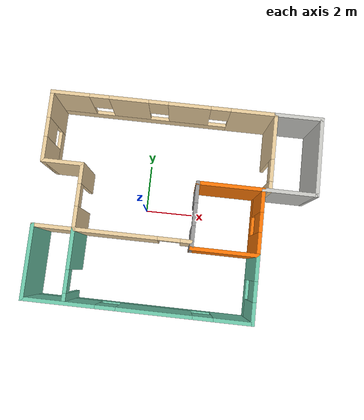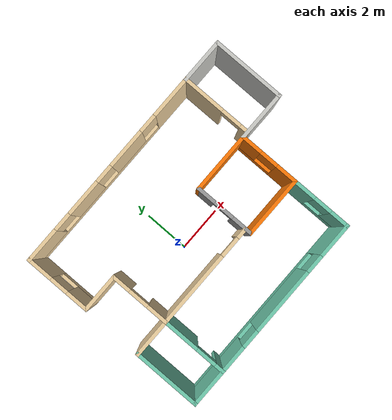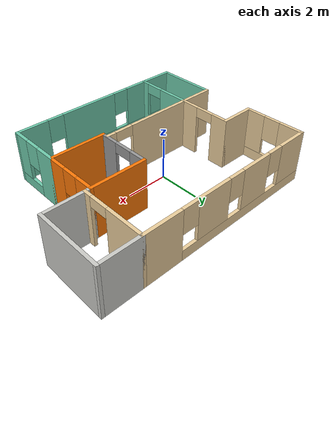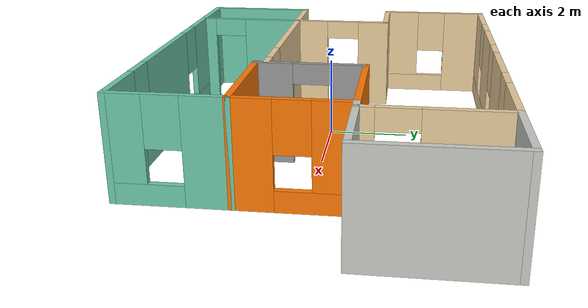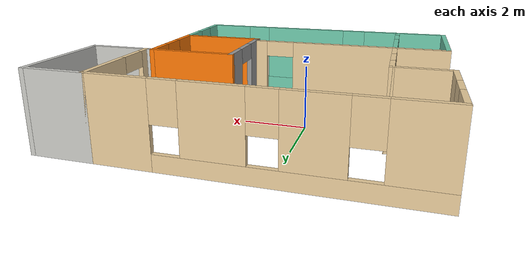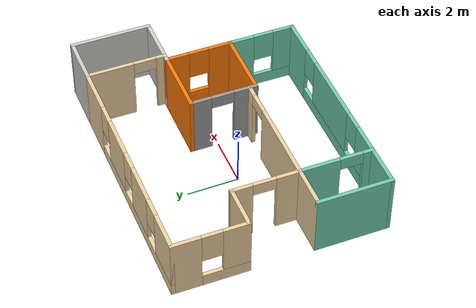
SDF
<?xml version='1.0'?>
<sdf version='1.6'>
  <model name='someHouse'>
    <link name='Wall_24'>
      <pose frame=''>3.375 -1.55 0 0 -0 0</pose>
      <self_collide>0</self_collide>
      <kinematic>0</kinematic>
      <visual name='Wall_24_Visual'>
        <pose frame=''>0 0 1.25 0 -0 0</pose>
        <geometry>
          <box>
            <size>2.75 0.15 2.5</size>
          </box>
        </geometry>
        <material>
          <script>
            <uri>file://media/materials/scripts/gazebo.material</uri>
            <name>Gazebo/Grey</name>
          </script>
          <ambient>0.996078 0.47451 0.0196078 1</ambient>
          <shader type='pixel'/>
          <diffuse>0.7 0.7 0.7 1</diffuse>
          <specular>0.01 0.01 0.01 1</specular>
          <emissive>0 0 0 1</emissive>
        </material>
        <meta>
          <layer>0</layer>
        </meta>
        <transparency>0</transparency>
        <cast_shadows>1</cast_shadows>
      </visual>
      <collision name='Wall_24_Collision'>
        <laser_retro>0</laser_retro>
        <max_contacts>10</max_contacts>
        <pose frame=''>0 0 1.25 0 -0 0</pose>
        <geometry>
          <box>
            <size>2.75 0.15 2.5</size>
          </box>
        </geometry>
        <surface>
          <friction>
            <ode>
              <mu>1</mu>
              <mu2>1</mu2>
              <fdir1>0 0 0</fdir1>
              <slip1>0</slip1>
              <slip2>0</slip2>
            </ode>
            <torsional>
              <coefficient>1</coefficient>
              <patch_radius>0</patch_radius>
              <surface_radius>0</surface_radius>
              <use_patch_radius>1</use_patch_radius>
              <ode>
                <slip>0</slip>
              </ode>
            </torsional>
          </friction>
          <bounce>
            <restitution_coefficient>0</restitution_coefficient>
            <threshold>1e+06</threshold>
          </bounce>
          <contact>
            <collide_without_contact>0</collide_without_contact>
            <collide_without_contact_bitmask>1</collide_without_contact_bitmask>
            <collide_bitmask>1</collide_bitmask>
            <ode>
              <soft_cfm>0</soft_cfm>
              <soft_erp>0.2</soft_erp>
              <kp>1e+13</kp>
              <kd>1</kd>
              <max_vel>0.01</max_vel>
              <min_depth>0</min_depth>
            </ode>
            <bullet>
              <split_impulse>1</split_impulse>
              <split_impulse_penetration_threshold>-0.01</split_impulse_penetration_threshold>
              <soft_cfm>0</soft_cfm>
              <soft_erp>0.2</soft_erp>
              <kp>1e+13</kp>
              <kd>1</kd>
            </bullet>
          </contact>
        </surface>
      </collision>
    </link>
    <link name='Wall_25'>
      <pose frame=''>4.675 -0.25 0 0 -0 1.5708</pose>
      <self_collide>0</self_collide>
      <kinematic>0</kinematic>
      <visual name='Wall_25_Visual_0'>
        <pose frame=''>-0.884286 0 1.25 0 -0 0</pose>
        <geometry>
          <box>
            <size>0.981427 0.15 2.5</size>
          </box>
        </geometry>
        <material>
          <script>
            <uri>file://media/materials/scripts/gazebo.material</uri>
            <name>Gazebo/Grey</name>
          </script>
          <ambient>0.996078 0.47451 0.0196078 1</ambient>
          <shader type='pixel'/>
          <diffuse>0.7 0.7 0.7 1</diffuse>
          <specular>0.01 0.01 0.01 1</specular>
          <emissive>0 0 0 1</emissive>
        </material>
        <meta>
          <layer>0</layer>
        </meta>
        <transparency>0</transparency>
        <cast_shadows>1</cast_shadows>
      </visual>
      <visual name='Wall_25_Visual_1'>
        <pose frame=''>0.490714 0 0.25 0 -0 0</pose>
        <geometry>
          <box>
            <size>1.76857 0.15 0.5</size>
          </box>
        </geometry>
        <material>
          <script>
            <uri>file://media/materials/scripts/gazebo.material</uri>
            <name>Gazebo/Grey</name>
          </script>
          <ambient>0.996078 0.47451 0.0196078 1</ambient>
          <shader type='pixel'/>
          <diffuse>0.7 0.7 0.7 1</diffuse>
          <specular>0.01 0.01 0.01 1</specular>
          <emissive>0 0 0 1</emissive>
        </material>
        <meta>
          <layer>0</layer>
        </meta>
        <transparency>0</transparency>
        <cast_shadows>1</cast_shadows>
      </visual>
      <visual name='Wall_25_Visual_2'>
        <pose frame=''>0.890714 0 1.5 0 -0 0</pose>
        <geometry>
          <box>
            <size>0.968573 0.15 2</size>
          </box>
        </geometry>
        <material>
          <script>
            <uri>file://media/materials/scripts/gazebo.material</uri>
            <name>Gazebo/Grey</name>
          </script>
          <ambient>0.996078 0.47451 0.0196078 1</ambient>
          <shader type='pixel'/>
          <diffuse>0.7 0.7 0.7 1</diffuse>
          <specular>0.01 0.01 0.01 1</specular>
          <emissive>0 0 0 1</emissive>
        </material>
        <meta>
          <layer>0</layer>
        </meta>
        <transparency>0</transparency>
        <cast_shadows>1</cast_shadows>
      </visual>
      <visual name='Wall_25_Visual_3'>
        <pose frame=''>0.006427 0 1.9 0 -0 0</pose>
        <geometry>
          <box>
            <size>0.8 0.15 1.2</size>
          </box>
        </geometry>
        <material>
          <script>
            <uri>file://media/materials/scripts/gazebo.material</uri>
            <name>Gazebo/Grey</name>
          </script>
          <ambient>0.996078 0.47451 0.0196078 1</ambient>
          <shader type='pixel'/>
          <diffuse>0.7 0.7 0.7 1</diffuse>
          <specular>0.01 0.01 0.01 1</specular>
          <emissive>0 0 0 1</emissive>
        </material>
        <meta>
          <layer>0</layer>
        </meta>
        <transparency>0</transparency>
        <cast_shadows>1</cast_shadows>
      </visual>
      <collision name='Wall_25_Collision_0'>
        <laser_retro>0</laser_retro>
        <max_contacts>10</max_contacts>
        <pose frame=''>-0.884286 0 1.25 0 -0 0</pose>
        <geometry>
          <box>
            <size>0.981427 0.15 2.5</size>
          </box>
        </geometry>
        <surface>
          <friction>
            <ode>
              <mu>1</mu>
              <mu2>1</mu2>
              <fdir1>0 0 0</fdir1>
              <slip1>0</slip1>
              <slip2>0</slip2>
            </ode>
            <torsional>
              <coefficient>1</coefficient>
              <patch_radius>0</patch_radius>
              <surface_radius>0</surface_radius>
              <use_patch_radius>1</use_patch_radius>
              <ode>
                <slip>0</slip>
              </ode>
            </torsional>
          </friction>
          <bounce>
            <restitution_coefficient>0</restitution_coefficient>
            <threshold>1e+06</threshold>
          </bounce>
          <contact>
            <collide_without_contact>0</collide_without_contact>
            <collide_without_contact_bitmask>1</collide_without_contact_bitmask>
            <collide_bitmask>1</collide_bitmask>
            <ode>
              <soft_cfm>0</soft_cfm>
              <soft_erp>0.2</soft_erp>
              <kp>1e+13</kp>
              <kd>1</kd>
              <max_vel>0.01</max_vel>
              <min_depth>0</min_depth>
            </ode>
            <bullet>
              <split_impulse>1</split_impulse>
              <split_impulse_penetration_threshold>-0.01</split_impulse_penetration_threshold>
              <soft_cfm>0</soft_cfm>
              <soft_erp>0.2</soft_erp>
              <kp>1e+13</kp>
              <kd>1</kd>
            </bullet>
          </contact>
        </surface>
      </collision>
      <collision name='Wall_25_Collision_1'>
        <laser_retro>0</laser_retro>
        <max_contacts>10</max_contacts>
        <pose frame=''>0.490714 0 0.25 0 -0 0</pose>
        <geometry>
          <box>
            <size>1.76857 0.15 0.5</size>
          </box>
        </geometry>
        <surface>
          <friction>
            <ode>
              <mu>1</mu>
              <mu2>1</mu2>
              <fdir1>0 0 0</fdir1>
              <slip1>0</slip1>
              <slip2>0</slip2>
            </ode>
            <torsional>
              <coefficient>1</coefficient>
              <patch_radius>0</patch_radius>
              <surface_radius>0</surface_radius>
              <use_patch_radius>1</use_patch_radius>
              <ode>
                <slip>0</slip>
              </ode>
            </torsional>
          </friction>
          <bounce>
            <restitution_coefficient>0</restitution_coefficient>
            <threshold>1e+06</threshold>
          </bounce>
          <contact>
            <collide_without_contact>0</collide_without_contact>
            <collide_without_contact_bitmask>1</collide_without_contact_bitmask>
            <collide_bitmask>1</collide_bitmask>
            <ode>
              <soft_cfm>0</soft_cfm>
              <soft_erp>0.2</soft_erp>
              <kp>1e+13</kp>
              <kd>1</kd>
              <max_vel>0.01</max_vel>
              <min_depth>0</min_depth>
            </ode>
            <bullet>
              <split_impulse>1</split_impulse>
              <split_impulse_penetration_threshold>-0.01</split_impulse_penetration_threshold>
              <soft_cfm>0</soft_cfm>
              <soft_erp>0.2</soft_erp>
              <kp>1e+13</kp>
              <kd>1</kd>
            </bullet>
          </contact>
        </surface>
      </collision>
      <collision name='Wall_25_Collision_2'>
        <laser_retro>0</laser_retro>
        <max_contacts>10</max_contacts>
        <pose frame=''>0.890714 0 1.5 0 -0 0</pose>
        <geometry>
          <box>
            <size>0.968573 0.15 2</size>
          </box>
        </geometry>
        <surface>
          <friction>
            <ode>
              <mu>1</mu>
              <mu2>1</mu2>
              <fdir1>0 0 0</fdir1>
              <slip1>0</slip1>
              <slip2>0</slip2>
            </ode>
            <torsional>
              <coefficient>1</coefficient>
              <patch_radius>0</patch_radius>
              <surface_radius>0</surface_radius>
              <use_patch_radius>1</use_patch_radius>
              <ode>
                <slip>0</slip>
              </ode>
            </torsional>
          </friction>
          <bounce>
            <restitution_coefficient>0</restitution_coefficient>
            <threshold>1e+06</threshold>
          </bounce>
          <contact>
            <collide_without_contact>0</collide_without_contact>
            <collide_without_contact_bitmask>1</collide_without_contact_bitmask>
            <collide_bitmask>1</collide_bitmask>
            <ode>
              <soft_cfm>0</soft_cfm>
              <soft_erp>0.2</soft_erp>
              <kp>1e+13</kp>
              <kd>1</kd>
              <max_vel>0.01</max_vel>
              <min_depth>0</min_depth>
            </ode>
            <bullet>
              <split_impulse>1</split_impulse>
              <split_impulse_penetration_threshold>-0.01</split_impulse_penetration_threshold>
              <soft_cfm>0</soft_cfm>
              <soft_erp>0.2</soft_erp>
              <kp>1e+13</kp>
              <kd>1</kd>
            </bullet>
          </contact>
        </surface>
      </collision>
      <collision name='Wall_25_Collision_3'>
        <laser_retro>0</laser_retro>
        <max_contacts>10</max_contacts>
        <pose frame=''>0.006427 0 1.9 0 -0 0</pose>
        <geometry>
          <box>
            <size>0.8 0.15 1.2</size>
          </box>
        </geometry>
        <surface>
          <friction>
            <ode>
              <mu>1</mu>
              <mu2>1</mu2>
              <fdir1>0 0 0</fdir1>
              <slip1>0</slip1>
              <slip2>0</slip2>
            </ode>
            <torsional>
              <coefficient>1</coefficient>
              <patch_radius>0</patch_radius>
              <surface_radius>0</surface_radius>
              <use_patch_radius>1</use_patch_radius>
              <ode>
                <slip>0</slip>
              </ode>
            </torsional>
          </friction>
          <bounce>
            <restitution_coefficient>0</restitution_coefficient>
            <threshold>1e+06</threshold>
          </bounce>
          <contact>
            <collide_without_contact>0</collide_without_contact>
            <collide_without_contact_bitmask>1</collide_without_contact_bitmask>
            <collide_bitmask>1</collide_bitmask>
            <ode>
              <soft_cfm>0</soft_cfm>
              <soft_erp>0.2</soft_erp>
              <kp>1e+13</kp>
              <kd>1</kd>
              <max_vel>0.01</max_vel>
              <min_depth>0</min_depth>
            </ode>
            <bullet>
              <split_impulse>1</split_impulse>
              <split_impulse_penetration_threshold>-0.01</split_impulse_penetration_threshold>
              <soft_cfm>0</soft_cfm>
              <soft_erp>0.2</soft_erp>
              <kp>1e+13</kp>
              <kd>1</kd>
            </bullet>
          </contact>
        </surface>
      </collision>
    </link>
    <link name='Wall_26'>
      <pose frame=''>3.375 1.05 0 0 -0 3.14159</pose>
      <self_collide>0</self_collide>
      <kinematic>0</kinematic>
      <visual name='Wall_26_Visual'>
        <pose frame=''>0 0 1.25 0 -0 0</pose>
        <geometry>
          <box>
            <size>2.75 0.15 2.5</size>
          </box>
        </geometry>
        <material>
          <script>
            <uri>file://media/materials/scripts/gazebo.material</uri>
            <name>Gazebo/Grey</name>
          </script>
          <ambient>0.996078 0.47451 0.0196078 1</ambient>
          <shader type='pixel'/>
          <diffuse>0.7 0.7 0.7 1</diffuse>
          <specular>0.01 0.01 0.01 1</specular>
          <emissive>0 0 0 1</emissive>
        </material>
        <meta>
          <layer>0</layer>
        </meta>
        <transparency>0</transparency>
        <cast_shadows>1</cast_shadows>
      </visual>
      <collision name='Wall_26_Collision'>
        <laser_retro>0</laser_retro>
        <max_contacts>10</max_contacts>
        <pose frame=''>0 0 1.25 0 -0 0</pose>
        <geometry>
          <box>
            <size>2.75 0.15 2.5</size>
          </box>
        </geometry>
        <surface>
          <friction>
            <ode>
              <mu>1</mu>
              <mu2>1</mu2>
              <fdir1>0 0 0</fdir1>
              <slip1>0</slip1>
              <slip2>0</slip2>
            </ode>
            <torsional>
              <coefficient>1</coefficient>
              <patch_radius>0</patch_radius>
              <surface_radius>0</surface_radius>
              <use_patch_radius>1</use_patch_radius>
              <ode>
                <slip>0</slip>
              </ode>
            </torsional>
          </friction>
          <bounce>
            <restitution_coefficient>0</restitution_coefficient>
            <threshold>1e+06</threshold>
          </bounce>
          <contact>
            <collide_without_contact>0</collide_without_contact>
            <collide_without_contact_bitmask>1</collide_without_contact_bitmask>
            <collide_bitmask>1</collide_bitmask>
            <ode>
              <soft_cfm>0</soft_cfm>
              <soft_erp>0.2</soft_erp>
              <kp>1e+13</kp>
              <kd>1</kd>
              <max_vel>0.01</max_vel>
              <min_depth>0</min_depth>
            </ode>
            <bullet>
              <split_impulse>1</split_impulse>
              <split_impulse_penetration_threshold>-0.01</split_impulse_penetration_threshold>
              <soft_cfm>0</soft_cfm>
              <soft_erp>0.2</soft_erp>
              <kp>1e+13</kp>
              <kd>1</kd>
            </bullet>
          </contact>
        </surface>
      </collision>
    </link>
    <link name='Wall_30'>
      <pose frame=''>2.075 -0.25 0 0 0 -1.5708</pose>
      <self_collide>0</self_collide>
      <kinematic>0</kinematic>
      <visual name='Wall_30_Visual_0'>
        <pose frame=''>-0.934617 0 1.25 0 -0 0</pose>
        <geometry>
          <box>
            <size>0.880765 0.15 2.5</size>
          </box>
        </geometry>
        <material>
          <script>
            <uri>file://media/materials/scripts/gazebo.material</uri>
            <name>Gazebo/Grey</name>
          </script>
          <ambient>1 1 1 1</ambient>
          <shader type='pixel'/>
          <diffuse>0.7 0.7 0.7 1</diffuse>
          <specular>0.01 0.01 0.01 1</specular>
          <emissive>0 0 0 1</emissive>
        </material>
        <meta>
          <layer>0</layer>
        </meta>
        <transparency>0</transparency>
        <cast_shadows>1</cast_shadows>
      </visual>
      <visual name='Wall_30_Visual_1'>
        <pose frame=''>0.890383 0 1.25 0 -0 0</pose>
        <geometry>
          <box>
            <size>0.969235 0.15 2.5</size>
          </box>
        </geometry>
        <material>
          <script>
            <uri>file://media/materials/scripts/gazebo.material</uri>
            <name>Gazebo/Grey</name>
          </script>
          <ambient>1 1 1 1</ambient>
          <shader type='pixel'/>
          <diffuse>0.7 0.7 0.7 1</diffuse>
          <specular>0.01 0.01 0.01 1</specular>
          <emissive>0 0 0 1</emissive>
        </material>
        <meta>
          <layer>0</layer>
        </meta>
        <transparency>0</transparency>
        <cast_shadows>1</cast_shadows>
      </visual>
      <visual name='Wall_30_Visual_2'>
        <pose frame=''>-0.044235 0 2.25 0 -0 0</pose>
        <geometry>
          <box>
            <size>0.9 0.15 0.5</size>
          </box>
        </geometry>
        <material>
          <script>
            <uri>file://media/materials/scripts/gazebo.material</uri>
            <name>Gazebo/Grey</name>
          </script>
          <ambient>1 1 1 1</ambient>
          <shader type='pixel'/>
          <diffuse>0.7 0.7 0.7 1</diffuse>
          <specular>0.01 0.01 0.01 1</specular>
          <emissive>0 0 0 1</emissive>
        </material>
        <meta>
          <layer>0</layer>
        </meta>
        <transparency>0</transparency>
        <cast_shadows>1</cast_shadows>
      </visual>
      <collision name='Wall_30_Collision_0'>
        <laser_retro>0</laser_retro>
        <max_contacts>10</max_contacts>
        <pose frame=''>-0.934617 0 1.25 0 -0 0</pose>
        <geometry>
          <box>
            <size>0.880765 0.15 2.5</size>
          </box>
        </geometry>
        <surface>
          <friction>
            <ode>
              <mu>1</mu>
              <mu2>1</mu2>
              <fdir1>0 0 0</fdir1>
              <slip1>0</slip1>
              <slip2>0</slip2>
            </ode>
            <torsional>
              <coefficient>1</coefficient>
              <patch_radius>0</patch_radius>
              <surface_radius>0</surface_radius>
              <use_patch_radius>1</use_patch_radius>
              <ode>
                <slip>0</slip>
              </ode>
            </torsional>
          </friction>
          <bounce>
            <restitution_coefficient>0</restitution_coefficient>
            <threshold>1e+06</threshold>
          </bounce>
          <contact>
            <collide_without_contact>0</collide_without_contact>
            <collide_without_contact_bitmask>1</collide_without_contact_bitmask>
            <collide_bitmask>1</collide_bitmask>
            <ode>
              <soft_cfm>0</soft_cfm>
              <soft_erp>0.2</soft_erp>
              <kp>1e+13</kp>
              <kd>1</kd>
              <max_vel>0.01</max_vel>
              <min_depth>0</min_depth>
            </ode>
            <bullet>
              <split_impulse>1</split_impulse>
              <split_impulse_penetration_threshold>-0.01</split_impulse_penetration_threshold>
              <soft_cfm>0</soft_cfm>
              <soft_erp>0.2</soft_erp>
              <kp>1e+13</kp>
              <kd>1</kd>
            </bullet>
          </contact>
        </surface>
      </collision>
      <collision name='Wall_30_Collision_1'>
        <laser_retro>0</laser_retro>
        <max_contacts>10</max_contacts>
        <pose frame=''>0.890383 0 1.25 0 -0 0</pose>
        <geometry>
          <box>
            <size>0.969235 0.15 2.5</size>
          </box>
        </geometry>
        <surface>
          <friction>
            <ode>
              <mu>1</mu>
              <mu2>1</mu2>
              <fdir1>0 0 0</fdir1>
              <slip1>0</slip1>
              <slip2>0</slip2>
            </ode>
            <torsional>
              <coefficient>1</coefficient>
              <patch_radius>0</patch_radius>
              <surface_radius>0</surface_radius>
              <use_patch_radius>1</use_patch_radius>
              <ode>
                <slip>0</slip>
              </ode>
            </torsional>
          </friction>
          <bounce>
            <restitution_coefficient>0</restitution_coefficient>
            <threshold>1e+06</threshold>
          </bounce>
          <contact>
            <collide_without_contact>0</collide_without_contact>
            <collide_without_contact_bitmask>1</collide_without_contact_bitmask>
            <collide_bitmask>1</collide_bitmask>
            <ode>
              <soft_cfm>0</soft_cfm>
              <soft_erp>0.2</soft_erp>
              <kp>1e+13</kp>
              <kd>1</kd>
              <max_vel>0.01</max_vel>
              <min_depth>0</min_depth>
            </ode>
            <bullet>
              <split_impulse>1</split_impulse>
              <split_impulse_penetration_threshold>-0.01</split_impulse_penetration_threshold>
              <soft_cfm>0</soft_cfm>
              <soft_erp>0.2</soft_erp>
              <kp>1e+13</kp>
              <kd>1</kd>
            </bullet>
          </contact>
        </surface>
      </collision>
      <collision name='Wall_30_Collision_2'>
        <laser_retro>0</laser_retro>
        <max_contacts>10</max_contacts>
        <pose frame=''>-0.044235 0 2.25 0 -0 0</pose>
        <geometry>
          <box>
            <size>0.9 0.15 0.5</size>
          </box>
        </geometry>
        <surface>
          <friction>
            <ode>
              <mu>1</mu>
              <mu2>1</mu2>
              <fdir1>0 0 0</fdir1>
              <slip1>0</slip1>
              <slip2>0</slip2>
            </ode>
            <torsional>
              <coefficient>1</coefficient>
              <patch_radius>0</patch_radius>
              <surface_radius>0</surface_radius>
              <use_patch_radius>1</use_patch_radius>
              <ode>
                <slip>0</slip>
              </ode>
            </torsional>
          </friction>
          <bounce>
            <restitution_coefficient>0</restitution_coefficient>
            <threshold>1e+06</threshold>
          </bounce>
          <contact>
            <collide_without_contact>0</collide_without_contact>
            <collide_without_contact_bitmask>1</collide_without_contact_bitmask>
            <collide_bitmask>1</collide_bitmask>
            <ode>
              <soft_cfm>0</soft_cfm>
              <soft_erp>0.2</soft_erp>
              <kp>1e+13</kp>
              <kd>1</kd>
              <max_vel>0.01</max_vel>
              <min_depth>0</min_depth>
            </ode>
            <bullet>
              <split_impulse>1</split_impulse>
              <split_impulse_penetration_threshold>-0.01</split_impulse_penetration_threshold>
              <soft_cfm>0</soft_cfm>
              <soft_erp>0.2</soft_erp>
              <kp>1e+13</kp>
              <kd>1</kd>
            </bullet>
          </contact>
        </surface>
      </collision>
    </link>
    <link name='Wall_32'>
      <pose frame=''>5.725 1.05 0 0 -0 0</pose>
      <self_collide>0</self_collide>
      <kinematic>0</kinematic>
      <visual name='Wall_32_Visual'>
        <pose frame=''>0 0 1.25 0 -0 0</pose>
        <geometry>
          <box>
            <size>2.25 0.15 2.5</size>
          </box>
        </geometry>
        <material>
          <script>
            <uri>file://media/materials/scripts/gazebo.material</uri>
            <name>Gazebo/CeilingTiled</name>
          </script>
          <ambient>0.760784 0.662745 0.627451 1</ambient>
          <shader type='pixel'/>
          <diffuse>1 1 1 1</diffuse>
          <specular>0 0 0 1</specular>
          <emissive>0 0 0 1</emissive>
        </material>
        <meta>
          <layer>0</layer>
        </meta>
        <transparency>0</transparency>
        <cast_shadows>1</cast_shadows>
      </visual>
      <collision name='Wall_32_Collision'>
        <laser_retro>0</laser_retro>
        <max_contacts>10</max_contacts>
        <pose frame=''>0 0 1.25 0 -0 0</pose>
        <geometry>
          <box>
            <size>2.25 0.15 2.5</size>
          </box>
        </geometry>
        <surface>
          <friction>
            <ode>
              <mu>1</mu>
              <mu2>1</mu2>
              <fdir1>0 0 0</fdir1>
              <slip1>0</slip1>
              <slip2>0</slip2>
            </ode>
            <torsional>
              <coefficient>1</coefficient>
              <patch_radius>0</patch_radius>
              <surface_radius>0</surface_radius>
              <use_patch_radius>1</use_patch_radius>
              <ode>
                <slip>0</slip>
              </ode>
            </torsional>
          </friction>
          <bounce>
            <restitution_coefficient>0</restitution_coefficient>
            <threshold>1e+06</threshold>
          </bounce>
          <contact>
            <collide_without_contact>0</collide_without_contact>
            <collide_without_contact_bitmask>1</collide_without_contact_bitmask>
            <collide_bitmask>1</collide_bitmask>
            <ode>
              <soft_cfm>0</soft_cfm>
              <soft_erp>0.2</soft_erp>
              <kp>1e+13</kp>
              <kd>1</kd>
              <max_vel>0.01</max_vel>
              <min_depth>0</min_depth>
            </ode>
            <bullet>
              <split_impulse>1</split_impulse>
              <split_impulse_penetration_threshold>-0.01</split_impulse_penetration_threshold>
              <soft_cfm>0</soft_cfm>
              <soft_erp>0.2</soft_erp>
              <kp>1e+13</kp>
              <kd>1</kd>
            </bullet>
          </contact>
        </surface>
      </collision>
    </link>
    <link name='Wall_33'>
      <pose frame=''>6.775 2.6 0 0 -0 1.5708</pose>
      <self_collide>0</self_collide>
      <kinematic>0</kinematic>
      <visual name='Wall_33_Visual'>
        <pose frame=''>0 0 1.25 0 -0 0</pose>
        <geometry>
          <box>
            <size>3.25 0.15 2.5</size>
          </box>
        </geometry>
        <material>
          <script>
            <uri>file://media/materials/scripts/gazebo.material</uri>
            <name>Gazebo/CeilingTiled</name>
          </script>
          <ambient>0.760784 0.662745 0.627451 1</ambient>
          <shader type='pixel'/>
          <diffuse>1 1 1 1</diffuse>
          <specular>0 0 0 1</specular>
          <emissive>0 0 0 1</emissive>
        </material>
        <meta>
          <layer>0</layer>
        </meta>
        <transparency>0</transparency>
        <cast_shadows>1</cast_shadows>
      </visual>
      <collision name='Wall_33_Collision'>
        <laser_retro>0</laser_retro>
        <max_contacts>10</max_contacts>
        <pose frame=''>0 0 1.25 0 -0 0</pose>
        <geometry>
          <box>
            <size>3.25 0.15 2.5</size>
          </box>
        </geometry>
        <surface>
          <friction>
            <ode>
              <mu>1</mu>
              <mu2>1</mu2>
              <fdir1>0 0 0</fdir1>
              <slip1>0</slip1>
              <slip2>0</slip2>
            </ode>
            <torsional>
              <coefficient>1</coefficient>
              <patch_radius>0</patch_radius>
              <surface_radius>0</surface_radius>
              <use_patch_radius>1</use_patch_radius>
              <ode>
                <slip>0</slip>
              </ode>
            </torsional>
          </friction>
          <bounce>
            <restitution_coefficient>0</restitution_coefficient>
            <threshold>1e+06</threshold>
          </bounce>
          <contact>
            <collide_without_contact>0</collide_without_contact>
            <collide_without_contact_bitmask>1</collide_without_contact_bitmask>
            <collide_bitmask>1</collide_bitmask>
            <ode>
              <soft_cfm>0</soft_cfm>
              <soft_erp>0.2</soft_erp>
              <kp>1e+13</kp>
              <kd>1</kd>
              <max_vel>0.01</max_vel>
              <min_depth>0</min_depth>
            </ode>
            <bullet>
              <split_impulse>1</split_impulse>
              <split_impulse_penetration_threshold>-0.01</split_impulse_penetration_threshold>
              <soft_cfm>0</soft_cfm>
              <soft_erp>0.2</soft_erp>
              <kp>1e+13</kp>
              <kd>1</kd>
            </bullet>
          </contact>
        </surface>
      </collision>
    </link>
    <link name='Wall_34'>
      <pose frame=''>5.85 4.15 0 0 -0 3.14159</pose>
      <self_collide>0</self_collide>
      <kinematic>0</kinematic>
      <visual name='Wall_34_Visual'>
        <pose frame=''>0 0 1.25 0 -0 0</pose>
        <geometry>
          <box>
            <size>2 0.15 2.5</size>
          </box>
        </geometry>
        <material>
          <script>
            <uri>file://media/materials/scripts/gazebo.material</uri>
            <name>Gazebo/CeilingTiled</name>
          </script>
          <ambient>0.760784 0.662745 0.627451 1</ambient>
          <shader type='pixel'/>
          <diffuse>1 1 1 1</diffuse>
          <specular>0 0 0 1</specular>
          <emissive>0 0 0 1</emissive>
        </material>
        <meta>
          <layer>0</layer>
        </meta>
        <transparency>0</transparency>
        <cast_shadows>1</cast_shadows>
      </visual>
      <collision name='Wall_34_Collision'>
        <laser_retro>0</laser_retro>
        <max_contacts>10</max_contacts>
        <pose frame=''>0 0 1.25 0 -0 0</pose>
        <geometry>
          <box>
            <size>2 0.15 2.5</size>
          </box>
        </geometry>
        <surface>
          <friction>
            <ode>
              <mu>1</mu>
              <mu2>1</mu2>
              <fdir1>0 0 0</fdir1>
              <slip1>0</slip1>
              <slip2>0</slip2>
            </ode>
            <torsional>
              <coefficient>1</coefficient>
              <patch_radius>0</patch_radius>
              <surface_radius>0</surface_radius>
              <use_patch_radius>1</use_patch_radius>
              <ode>
                <slip>0</slip>
              </ode>
            </torsional>
          </friction>
          <bounce>
            <restitution_coefficient>0</restitution_coefficient>
            <threshold>1e+06</threshold>
          </bounce>
          <contact>
            <collide_without_contact>0</collide_without_contact>
            <collide_without_contact_bitmask>1</collide_without_contact_bitmask>
            <collide_bitmask>1</collide_bitmask>
            <ode>
              <soft_cfm>0</soft_cfm>
              <soft_erp>0.2</soft_erp>
              <kp>1e+13</kp>
              <kd>1</kd>
              <max_vel>0.01</max_vel>
              <min_depth>0</min_depth>
            </ode>
            <bullet>
              <split_impulse>1</split_impulse>
              <split_impulse_penetration_threshold>-0.01</split_impulse_penetration_threshold>
              <soft_cfm>0</soft_cfm>
              <soft_erp>0.2</soft_erp>
              <kp>1e+13</kp>
              <kd>1</kd>
            </bullet>
          </contact>
        </surface>
      </collision>
    </link>
    <link name='Wall_35'>
      <pose frame=''>4.925 2.6 0 0 0 -1.5708</pose>
      <self_collide>0</self_collide>
      <kinematic>0</kinematic>
      <visual name='Wall_35_Visual_0'>
        <pose frame=''>-0.668512 0 1.25 0 -0 0</pose>
        <geometry>
          <box>
            <size>1.91298 0.15 2.5</size>
          </box>
        </geometry>
        <material>
          <script>
            <uri>file://media/materials/scripts/gazebo.material</uri>
            <name>Gazebo/Grey</name>
          </script>
          <ambient>0.921569 0.807843 0.615686 1</ambient>
          <shader type='pixel'/>
          <diffuse>0.7 0.7 0.7 1</diffuse>
          <specular>0.01 0.01 0.01 1</specular>
          <emissive>0 0 0 1</emissive>
        </material>
        <meta>
          <layer>0</layer>
        </meta>
        <transparency>0</transparency>
        <cast_shadows>1</cast_shadows>
      </visual>
      <visual name='Wall_35_Visual_1'>
        <pose frame=''>1.40649 0 1.25 0 -0 0</pose>
        <geometry>
          <box>
            <size>0.437025 0.15 2.5</size>
          </box>
        </geometry>
        <material>
          <script>
            <uri>file://media/materials/scripts/gazebo.material</uri>
            <name>Gazebo/Grey</name>
          </script>
          <ambient>0.921569 0.807843 0.615686 1</ambient>
          <shader type='pixel'/>
          <diffuse>0.7 0.7 0.7 1</diffuse>
          <specular>0.01 0.01 0.01 1</specular>
          <emissive>0 0 0 1</emissive>
        </material>
        <meta>
          <layer>0</layer>
        </meta>
        <transparency>0</transparency>
        <cast_shadows>1</cast_shadows>
      </visual>
      <visual name='Wall_35_Visual_2'>
        <pose frame=''>0.737975 0 2.25 0 -0 0</pose>
        <geometry>
          <box>
            <size>0.9 0.15 0.5</size>
          </box>
        </geometry>
        <material>
          <script>
            <uri>file://media/materials/scripts/gazebo.material</uri>
            <name>Gazebo/Grey</name>
          </script>
          <ambient>0.921569 0.807843 0.615686 1</ambient>
          <shader type='pixel'/>
          <diffuse>0.7 0.7 0.7 1</diffuse>
          <specular>0.01 0.01 0.01 1</specular>
          <emissive>0 0 0 1</emissive>
        </material>
        <meta>
          <layer>0</layer>
        </meta>
        <transparency>0</transparency>
        <cast_shadows>1</cast_shadows>
      </visual>
      <collision name='Wall_35_Collision_0'>
        <laser_retro>0</laser_retro>
        <max_contacts>10</max_contacts>
        <pose frame=''>-0.668512 0 1.25 0 -0 0</pose>
        <geometry>
          <box>
            <size>1.91298 0.15 2.5</size>
          </box>
        </geometry>
        <surface>
          <friction>
            <ode>
              <mu>1</mu>
              <mu2>1</mu2>
              <fdir1>0 0 0</fdir1>
              <slip1>0</slip1>
              <slip2>0</slip2>
            </ode>
            <torsional>
              <coefficient>1</coefficient>
              <patch_radius>0</patch_radius>
              <surface_radius>0</surface_radius>
              <use_patch_radius>1</use_patch_radius>
              <ode>
                <slip>0</slip>
              </ode>
            </torsional>
          </friction>
          <bounce>
            <restitution_coefficient>0</restitution_coefficient>
            <threshold>1e+06</threshold>
          </bounce>
          <contact>
            <collide_without_contact>0</collide_without_contact>
            <collide_without_contact_bitmask>1</collide_without_contact_bitmask>
            <collide_bitmask>1</collide_bitmask>
            <ode>
              <soft_cfm>0</soft_cfm>
              <soft_erp>0.2</soft_erp>
              <kp>1e+13</kp>
              <kd>1</kd>
              <max_vel>0.01</max_vel>
              <min_depth>0</min_depth>
            </ode>
            <bullet>
              <split_impulse>1</split_impulse>
              <split_impulse_penetration_threshold>-0.01</split_impulse_penetration_threshold>
              <soft_cfm>0</soft_cfm>
              <soft_erp>0.2</soft_erp>
              <kp>1e+13</kp>
              <kd>1</kd>
            </bullet>
          </contact>
        </surface>
      </collision>
      <collision name='Wall_35_Collision_1'>
        <laser_retro>0</laser_retro>
        <max_contacts>10</max_contacts>
        <pose frame=''>1.40649 0 1.25 0 -0 0</pose>
        <geometry>
          <box>
            <size>0.437025 0.15 2.5</size>
          </box>
        </geometry>
        <surface>
          <friction>
            <ode>
              <mu>1</mu>
              <mu2>1</mu2>
              <fdir1>0 0 0</fdir1>
              <slip1>0</slip1>
              <slip2>0</slip2>
            </ode>
            <torsional>
              <coefficient>1</coefficient>
              <patch_radius>0</patch_radius>
              <surface_radius>0</surface_radius>
              <use_patch_radius>1</use_patch_radius>
              <ode>
                <slip>0</slip>
              </ode>
            </torsional>
          </friction>
          <bounce>
            <restitution_coefficient>0</restitution_coefficient>
            <threshold>1e+06</threshold>
          </bounce>
          <contact>
            <collide_without_contact>0</collide_without_contact>
            <collide_without_contact_bitmask>1</collide_without_contact_bitmask>
            <collide_bitmask>1</collide_bitmask>
            <ode>
              <soft_cfm>0</soft_cfm>
              <soft_erp>0.2</soft_erp>
              <kp>1e+13</kp>
              <kd>1</kd>
              <max_vel>0.01</max_vel>
              <min_depth>0</min_depth>
            </ode>
            <bullet>
              <split_impulse>1</split_impulse>
              <split_impulse_penetration_threshold>-0.01</split_impulse_penetration_threshold>
              <soft_cfm>0</soft_cfm>
              <soft_erp>0.2</soft_erp>
              <kp>1e+13</kp>
              <kd>1</kd>
            </bullet>
          </contact>
        </surface>
      </collision>
      <collision name='Wall_35_Collision_2'>
        <laser_retro>0</laser_retro>
        <max_contacts>10</max_contacts>
        <pose frame=''>0.737975 0 2.25 0 -0 0</pose>
        <geometry>
          <box>
            <size>0.9 0.15 0.5</size>
          </box>
        </geometry>
        <surface>
          <friction>
            <ode>
              <mu>1</mu>
              <mu2>1</mu2>
              <fdir1>0 0 0</fdir1>
              <slip1>0</slip1>
              <slip2>0</slip2>
            </ode>
            <torsional>
              <coefficient>1</coefficient>
              <patch_radius>0</patch_radius>
              <surface_radius>0</surface_radius>
              <use_patch_radius>1</use_patch_radius>
              <ode>
                <slip>0</slip>
              </ode>
            </torsional>
          </friction>
          <bounce>
            <restitution_coefficient>0</restitution_coefficient>
            <threshold>1e+06</threshold>
          </bounce>
          <contact>
            <collide_without_contact>0</collide_without_contact>
            <collide_without_contact_bitmask>1</collide_without_contact_bitmask>
            <collide_bitmask>1</collide_bitmask>
            <ode>
              <soft_cfm>0</soft_cfm>
              <soft_erp>0.2</soft_erp>
              <kp>1e+13</kp>
              <kd>1</kd>
              <max_vel>0.01</max_vel>
              <min_depth>0</min_depth>
            </ode>
            <bullet>
              <split_impulse>1</split_impulse>
              <split_impulse_penetration_threshold>-0.01</split_impulse_penetration_threshold>
              <soft_cfm>0</soft_cfm>
              <soft_erp>0.2</soft_erp>
              <kp>1e+13</kp>
              <kd>1</kd>
            </bullet>
          </contact>
        </surface>
      </collision>
    </link>
    <link name='Wall_37'>
      <pose frame=''>0.375 4.15 0 0 -0 3.14159</pose>
      <self_collide>0</self_collide>
      <kinematic>0</kinematic>
      <visual name='Wall_37_Visual_0'>
        <pose frame=''>-3.66804 0 1.25 0 -0 0</pose>
        <geometry>
          <box>
            <size>1.91392 0.15 2.5</size>
          </box>
        </geometry>
        <material>
          <script>
            <uri>file://media/materials/scripts/gazebo.material</uri>
            <name>Gazebo/Grey</name>
          </script>
          <ambient>0.921569 0.807843 0.615686 1</ambient>
          <shader type='pixel'/>
          <diffuse>0.7 0.7 0.7 1</diffuse>
          <specular>0.01 0.01 0.01 1</specular>
          <emissive>0 0 0 1</emissive>
        </material>
        <meta>
          <layer>0</layer>
        </meta>
        <transparency>0</transparency>
        <cast_shadows>1</cast_shadows>
      </visual>
      <visual name='Wall_37_Visual_1'>
        <pose frame=''>0.95696 0 0.25 0 -0 0</pose>
        <geometry>
          <box>
            <size>7.33608 0.15 0.5</size>
          </box>
        </geometry>
        <material>
          <script>
            <uri>file://media/materials/scripts/gazebo.material</uri>
            <name>Gazebo/Grey</name>
          </script>
          <ambient>0.921569 0.807843 0.615686 1</ambient>
          <shader type='pixel'/>
          <diffuse>0.7 0.7 0.7 1</diffuse>
          <specular>0.01 0.01 0.01 1</specular>
          <emissive>0 0 0 1</emissive>
        </material>
        <meta>
          <layer>0</layer>
        </meta>
        <transparency>0</transparency>
        <cast_shadows>1</cast_shadows>
      </visual>
      <visual name='Wall_37_Visual_2'>
        <pose frame=''>-1.04305 0 1.5 0 -0 0</pose>
        <geometry>
          <box>
            <size>1.73606 0.15 2</size>
          </box>
        </geometry>
        <material>
          <script>
            <uri>file://media/materials/scripts/gazebo.material</uri>
            <name>Gazebo/Grey</name>
          </script>
          <ambient>0.921569 0.807843 0.615686 1</ambient>
          <shader type='pixel'/>
          <diffuse>0.7 0.7 0.7 1</diffuse>
          <specular>0.01 0.01 0.01 1</specular>
          <emissive>0 0 0 1</emissive>
        </material>
        <meta>
          <layer>0</layer>
        </meta>
        <transparency>0</transparency>
        <cast_shadows>1</cast_shadows>
      </visual>
      <visual name='Wall_37_Visual_3'>
        <pose frame=''>1.43179 0 1.5 0 -0 0</pose>
        <geometry>
          <box>
            <size>1.61363 0.15 2</size>
          </box>
        </geometry>
        <material>
          <script>
            <uri>file://media/materials/scripts/gazebo.material</uri>
            <name>Gazebo/Grey</name>
          </script>
          <ambient>0.921569 0.807843 0.615686 1</ambient>
          <shader type='pixel'/>
          <diffuse>0.7 0.7 0.7 1</diffuse>
          <specular>0.01 0.01 0.01 1</specular>
          <emissive>0 0 0 1</emissive>
        </material>
        <meta>
          <layer>0</layer>
        </meta>
        <transparency>0</transparency>
        <cast_shadows>1</cast_shadows>
      </visual>
      <visual name='Wall_37_Visual_4'>
        <pose frame=''>3.8318 0 1.5 0 -0 0</pose>
        <geometry>
          <box>
            <size>1.58639 0.15 2</size>
          </box>
        </geometry>
        <material>
          <script>
            <uri>file://media/materials/scripts/gazebo.material</uri>
            <name>Gazebo/Grey</name>
          </script>
          <ambient>0.921569 0.807843 0.615686 1</ambient>
          <shader type='pixel'/>
          <diffuse>0.7 0.7 0.7 1</diffuse>
          <specular>0.01 0.01 0.01 1</specular>
          <emissive>0 0 0 1</emissive>
        </material>
        <meta>
          <layer>0</layer>
        </meta>
        <transparency>0</transparency>
        <cast_shadows>1</cast_shadows>
      </visual>
      <visual name='Wall_37_Visual_5'>
        <pose frame=''>-2.31108 0 1.9 0 -0 0</pose>
        <geometry>
          <box>
            <size>0.8 0.15 1.2</size>
          </box>
        </geometry>
        <material>
          <script>
            <uri>file://media/materials/scripts/gazebo.material</uri>
            <name>Gazebo/Grey</name>
          </script>
          <ambient>0.921569 0.807843 0.615686 1</ambient>
          <shader type='pixel'/>
          <diffuse>0.7 0.7 0.7 1</diffuse>
          <specular>0.01 0.01 0.01 1</specular>
          <emissive>0 0 0 1</emissive>
        </material>
        <meta>
          <layer>0</layer>
        </meta>
        <transparency>0</transparency>
        <cast_shadows>1</cast_shadows>
      </visual>
      <visual name='Wall_37_Visual_6'>
        <pose frame=''>0.224979 0 1.9 0 -0 0</pose>
        <geometry>
          <box>
            <size>0.8 0.15 1.2</size>
          </box>
        </geometry>
        <material>
          <script>
            <uri>file://media/materials/scripts/gazebo.material</uri>
            <name>Gazebo/Grey</name>
          </script>
          <ambient>0.921569 0.807843 0.615686 1</ambient>
          <shader type='pixel'/>
          <diffuse>0.7 0.7 0.7 1</diffuse>
          <specular>0.01 0.01 0.01 1</specular>
          <emissive>0 0 0 1</emissive>
        </material>
        <meta>
          <layer>0</layer>
        </meta>
        <transparency>0</transparency>
        <cast_shadows>1</cast_shadows>
      </visual>
      <visual name='Wall_37_Visual_7'>
        <pose frame=''>2.63861 0 1.9 0 -0 0</pose>
        <geometry>
          <box>
            <size>0.8 0.15 1.2</size>
          </box>
        </geometry>
        <material>
          <script>
            <uri>file://media/materials/scripts/gazebo.material</uri>
            <name>Gazebo/Grey</name>
          </script>
          <ambient>0.921569 0.807843 0.615686 1</ambient>
          <shader type='pixel'/>
          <diffuse>0.7 0.7 0.7 1</diffuse>
          <specular>0.01 0.01 0.01 1</specular>
          <emissive>0 0 0 1</emissive>
        </material>
        <meta>
          <layer>0</layer>
        </meta>
        <transparency>0</transparency>
        <cast_shadows>1</cast_shadows>
      </visual>
      <collision name='Wall_37_Collision_0'>
        <laser_retro>0</laser_retro>
        <max_contacts>10</max_contacts>
        <pose frame=''>-3.66804 0 1.25 0 -0 0</pose>
        <geometry>
          <box>
            <size>1.91392 0.15 2.5</size>
          </box>
        </geometry>
        <surface>
          <friction>
            <ode>
              <mu>1</mu>
              <mu2>1</mu2>
              <fdir1>0 0 0</fdir1>
              <slip1>0</slip1>
              <slip2>0</slip2>
            </ode>
            <torsional>
              <coefficient>1</coefficient>
              <patch_radius>0</patch_radius>
              <surface_radius>0</surface_radius>
              <use_patch_radius>1</use_patch_radius>
              <ode>
                <slip>0</slip>
              </ode>
            </torsional>
          </friction>
          <bounce>
            <restitution_coefficient>0</restitution_coefficient>
            <threshold>1e+06</threshold>
          </bounce>
          <contact>
            <collide_without_contact>0</collide_without_contact>
            <collide_without_contact_bitmask>1</collide_without_contact_bitmask>
            <collide_bitmask>1</collide_bitmask>
            <ode>
              <soft_cfm>0</soft_cfm>
              <soft_erp>0.2</soft_erp>
              <kp>1e+13</kp>
              <kd>1</kd>
              <max_vel>0.01</max_vel>
              <min_depth>0</min_depth>
            </ode>
            <bullet>
              <split_impulse>1</split_impulse>
              <split_impulse_penetration_threshold>-0.01</split_impulse_penetration_threshold>
              <soft_cfm>0</soft_cfm>
              <soft_erp>0.2</soft_erp>
              <kp>1e+13</kp>
              <kd>1</kd>
            </bullet>
          </contact>
        </surface>
      </collision>
      <collision name='Wall_37_Collision_1'>
        <laser_retro>0</laser_retro>
        <max_contacts>10</max_contacts>
        <pose frame=''>0.95696 0 0.25 0 -0 0</pose>
        <geometry>
          <box>
            <size>7.33608 0.15 0.5</size>
          </box>
        </geometry>
        <surface>
          <friction>
            <ode>
              <mu>1</mu>
              <mu2>1</mu2>
              <fdir1>0 0 0</fdir1>
              <slip1>0</slip1>
              <slip2>0</slip2>
            </ode>
            <torsional>
              <coefficient>1</coefficient>
              <patch_radius>0</patch_radius>
              <surface_radius>0</surface_radius>
              <use_patch_radius>1</use_patch_radius>
              <ode>
                <slip>0</slip>
              </ode>
            </torsional>
          </friction>
          <bounce>
            <restitution_coefficient>0</restitution_coefficient>
            <threshold>1e+06</threshold>
          </bounce>
          <contact>
            <collide_without_contact>0</collide_without_contact>
            <collide_without_contact_bitmask>1</collide_without_contact_bitmask>
            <collide_bitmask>1</collide_bitmask>
            <ode>
              <soft_cfm>0</soft_cfm>
              <soft_erp>0.2</soft_erp>
              <kp>1e+13</kp>
              <kd>1</kd>
              <max_vel>0.01</max_vel>
              <min_depth>0</min_depth>
            </ode>
            <bullet>
              <split_impulse>1</split_impulse>
              <split_impulse_penetration_threshold>-0.01</split_impulse_penetration_threshold>
              <soft_cfm>0</soft_cfm>
              <soft_erp>0.2</soft_erp>
              <kp>1e+13</kp>
              <kd>1</kd>
            </bullet>
          </contact>
        </surface>
      </collision>
      <collision name='Wall_37_Collision_2'>
        <laser_retro>0</laser_retro>
        <max_contacts>10</max_contacts>
        <pose frame=''>-1.04305 0 1.5 0 -0 0</pose>
        <geometry>
          <box>
            <size>1.73606 0.15 2</size>
          </box>
        </geometry>
        <surface>
          <friction>
            <ode>
              <mu>1</mu>
              <mu2>1</mu2>
              <fdir1>0 0 0</fdir1>
              <slip1>0</slip1>
              <slip2>0</slip2>
            </ode>
            <torsional>
              <coefficient>1</coefficient>
              <patch_radius>0</patch_radius>
              <surface_radius>0</surface_radius>
              <use_patch_radius>1</use_patch_radius>
              <ode>
                <slip>0</slip>
              </ode>
            </torsional>
          </friction>
          <bounce>
            <restitution_coefficient>0</restitution_coefficient>
            <threshold>1e+06</threshold>
          </bounce>
          <contact>
            <collide_without_contact>0</collide_without_contact>
            <collide_without_contact_bitmask>1</collide_without_contact_bitmask>
            <collide_bitmask>1</collide_bitmask>
            <ode>
              <soft_cfm>0</soft_cfm>
              <soft_erp>0.2</soft_erp>
              <kp>1e+13</kp>
              <kd>1</kd>
              <max_vel>0.01</max_vel>
              <min_depth>0</min_depth>
            </ode>
            <bullet>
              <split_impulse>1</split_impulse>
              <split_impulse_penetration_threshold>-0.01</split_impulse_penetration_threshold>
              <soft_cfm>0</soft_cfm>
              <soft_erp>0.2</soft_erp>
              <kp>1e+13</kp>
              <kd>1</kd>
            </bullet>
          </contact>
        </surface>
      </collision>
      <collision name='Wall_37_Collision_3'>
        <laser_retro>0</laser_retro>
        <max_contacts>10</max_contacts>
        <pose frame=''>1.43179 0 1.5 0 -0 0</pose>
        <geometry>
          <box>
            <size>1.61363 0.15 2</size>
          </box>
        </geometry>
        <surface>
          <friction>
            <ode>
              <mu>1</mu>
              <mu2>1</mu2>
              <fdir1>0 0 0</fdir1>
              <slip1>0</slip1>
              <slip2>0</slip2>
            </ode>
            <torsional>
              <coefficient>1</coefficient>
              <patch_radius>0</patch_radius>
              <surface_radius>0</surface_radius>
              <use_patch_radius>1</use_patch_radius>
              <ode>
                <slip>0</slip>
              </ode>
            </torsional>
          </friction>
          <bounce>
            <restitution_coefficient>0</restitution_coefficient>
            <threshold>1e+06</threshold>
          </bounce>
          <contact>
            <collide_without_contact>0</collide_without_contact>
            <collide_without_contact_bitmask>1</collide_without_contact_bitmask>
            <collide_bitmask>1</collide_bitmask>
            <ode>
              <soft_cfm>0</soft_cfm>
              <soft_erp>0.2</soft_erp>
              <kp>1e+13</kp>
              <kd>1</kd>
              <max_vel>0.01</max_vel>
              <min_depth>0</min_depth>
            </ode>
            <bullet>
              <split_impulse>1</split_impulse>
              <split_impulse_penetration_threshold>-0.01</split_impulse_penetration_threshold>
              <soft_cfm>0</soft_cfm>
              <soft_erp>0.2</soft_erp>
              <kp>1e+13</kp>
              <kd>1</kd>
            </bullet>
          </contact>
        </surface>
      </collision>
      <collision name='Wall_37_Collision_4'>
        <laser_retro>0</laser_retro>
        <max_contacts>10</max_contacts>
        <pose frame=''>3.8318 0 1.5 0 -0 0</pose>
        <geometry>
          <box>
            <size>1.58639 0.15 2</size>
          </box>
        </geometry>
        <surface>
          <friction>
            <ode>
              <mu>1</mu>
              <mu2>1</mu2>
              <fdir1>0 0 0</fdir1>
              <slip1>0</slip1>
              <slip2>0</slip2>
            </ode>
            <torsional>
              <coefficient>1</coefficient>
              <patch_radius>0</patch_radius>
              <surface_radius>0</surface_radius>
              <use_patch_radius>1</use_patch_radius>
              <ode>
                <slip>0</slip>
              </ode>
            </torsional>
          </friction>
          <bounce>
            <restitution_coefficient>0</restitution_coefficient>
            <threshold>1e+06</threshold>
          </bounce>
          <contact>
            <collide_without_contact>0</collide_without_contact>
            <collide_without_contact_bitmask>1</collide_without_contact_bitmask>
            <collide_bitmask>1</collide_bitmask>
            <ode>
              <soft_cfm>0</soft_cfm>
              <soft_erp>0.2</soft_erp>
              <kp>1e+13</kp>
              <kd>1</kd>
              <max_vel>0.01</max_vel>
              <min_depth>0</min_depth>
            </ode>
            <bullet>
              <split_impulse>1</split_impulse>
              <split_impulse_penetration_threshold>-0.01</split_impulse_penetration_threshold>
              <soft_cfm>0</soft_cfm>
              <soft_erp>0.2</soft_erp>
              <kp>1e+13</kp>
              <kd>1</kd>
            </bullet>
          </contact>
        </surface>
      </collision>
      <collision name='Wall_37_Collision_5'>
        <laser_retro>0</laser_retro>
        <max_contacts>10</max_contacts>
        <pose frame=''>-2.31108 0 1.9 0 -0 0</pose>
        <geometry>
          <box>
            <size>0.8 0.15 1.2</size>
          </box>
        </geometry>
        <surface>
          <friction>
            <ode>
              <mu>1</mu>
              <mu2>1</mu2>
              <fdir1>0 0 0</fdir1>
              <slip1>0</slip1>
              <slip2>0</slip2>
            </ode>
            <torsional>
              <coefficient>1</coefficient>
              <patch_radius>0</patch_radius>
              <surface_radius>0</surface_radius>
              <use_patch_radius>1</use_patch_radius>
              <ode>
                <slip>0</slip>
              </ode>
            </torsional>
          </friction>
          <bounce>
            <restitution_coefficient>0</restitution_coefficient>
            <threshold>1e+06</threshold>
          </bounce>
          <contact>
            <collide_without_contact>0</collide_without_contact>
            <collide_without_contact_bitmask>1</collide_without_contact_bitmask>
            <collide_bitmask>1</collide_bitmask>
            <ode>
              <soft_cfm>0</soft_cfm>
              <soft_erp>0.2</soft_erp>
              <kp>1e+13</kp>
              <kd>1</kd>
              <max_vel>0.01</max_vel>
              <min_depth>0</min_depth>
            </ode>
            <bullet>
              <split_impulse>1</split_impulse>
              <split_impulse_penetration_threshold>-0.01</split_impulse_penetration_threshold>
              <soft_cfm>0</soft_cfm>
              <soft_erp>0.2</soft_erp>
              <kp>1e+13</kp>
              <kd>1</kd>
            </bullet>
          </contact>
        </surface>
      </collision>
      <collision name='Wall_37_Collision_6'>
        <laser_retro>0</laser_retro>
        <max_contacts>10</max_contacts>
        <pose frame=''>0.224979 0 1.9 0 -0 0</pose>
        <geometry>
          <box>
            <size>0.8 0.15 1.2</size>
          </box>
        </geometry>
        <surface>
          <friction>
            <ode>
              <mu>1</mu>
              <mu2>1</mu2>
              <fdir1>0 0 0</fdir1>
              <slip1>0</slip1>
              <slip2>0</slip2>
            </ode>
            <torsional>
              <coefficient>1</coefficient>
              <patch_radius>0</patch_radius>
              <surface_radius>0</surface_radius>
              <use_patch_radius>1</use_patch_radius>
              <ode>
                <slip>0</slip>
              </ode>
            </torsional>
          </friction>
          <bounce>
            <restitution_coefficient>0</restitution_coefficient>
            <threshold>1e+06</threshold>
          </bounce>
          <contact>
            <collide_without_contact>0</collide_without_contact>
            <collide_without_contact_bitmask>1</collide_without_contact_bitmask>
            <collide_bitmask>1</collide_bitmask>
            <ode>
              <soft_cfm>0</soft_cfm>
              <soft_erp>0.2</soft_erp>
              <kp>1e+13</kp>
              <kd>1</kd>
              <max_vel>0.01</max_vel>
              <min_depth>0</min_depth>
            </ode>
            <bullet>
              <split_impulse>1</split_impulse>
              <split_impulse_penetration_threshold>-0.01</split_impulse_penetration_threshold>
              <soft_cfm>0</soft_cfm>
              <soft_erp>0.2</soft_erp>
              <kp>1e+13</kp>
              <kd>1</kd>
            </bullet>
          </contact>
        </surface>
      </collision>
      <collision name='Wall_37_Collision_7'>
        <laser_retro>0</laser_retro>
        <max_contacts>10</max_contacts>
        <pose frame=''>2.63861 0 1.9 0 -0 0</pose>
        <geometry>
          <box>
            <size>0.8 0.15 1.2</size>
          </box>
        </geometry>
        <surface>
          <friction>
            <ode>
              <mu>1</mu>
              <mu2>1</mu2>
              <fdir1>0 0 0</fdir1>
              <slip1>0</slip1>
              <slip2>0</slip2>
            </ode>
            <torsional>
              <coefficient>1</coefficient>
              <patch_radius>0</patch_radius>
              <surface_radius>0</surface_radius>
              <use_patch_radius>1</use_patch_radius>
              <ode>
                <slip>0</slip>
              </ode>
            </torsional>
          </friction>
          <bounce>
            <restitution_coefficient>0</restitution_coefficient>
            <threshold>1e+06</threshold>
          </bounce>
          <contact>
            <collide_without_contact>0</collide_without_contact>
            <collide_without_contact_bitmask>1</collide_without_contact_bitmask>
            <collide_bitmask>1</collide_bitmask>
            <ode>
              <soft_cfm>0</soft_cfm>
              <soft_erp>0.2</soft_erp>
              <kp>1e+13</kp>
              <kd>1</kd>
              <max_vel>0.01</max_vel>
              <min_depth>0</min_depth>
            </ode>
            <bullet>
              <split_impulse>1</split_impulse>
              <split_impulse_penetration_threshold>-0.01</split_impulse_penetration_threshold>
              <soft_cfm>0</soft_cfm>
              <soft_erp>0.2</soft_erp>
              <kp>1e+13</kp>
              <kd>1</kd>
            </bullet>
          </contact>
        </surface>
      </collision>
    </link>
    <link name='Wall_38'>
      <pose frame=''>-4.175 2.725 0 0 0 -1.5708</pose>
      <self_collide>0</self_collide>
      <kinematic>0</kinematic>
      <visual name='Wall_38_Visual_0'>
        <pose frame=''>-0.917775 0 1.25 0 -0 0</pose>
        <geometry>
          <box>
            <size>1.16445 0.15 2.5</size>
          </box>
        </geometry>
        <material>
          <script>
            <uri>file://media/materials/scripts/gazebo.material</uri>
            <name>Gazebo/Grey</name>
          </script>
          <ambient>0.921569 0.807843 0.615686 1</ambient>
          <shader type='pixel'/>
          <diffuse>0.7 0.7 0.7 1</diffuse>
          <specular>0.01 0.01 0.01 1</specular>
          <emissive>0 0 0 1</emissive>
        </material>
        <meta>
          <layer>0</layer>
        </meta>
        <transparency>0</transparency>
        <cast_shadows>1</cast_shadows>
      </visual>
      <visual name='Wall_38_Visual_1'>
        <pose frame=''>0.582225 0 0.25 0 -0 0</pose>
        <geometry>
          <box>
            <size>1.83555 0.15 0.5</size>
          </box>
        </geometry>
        <material>
          <script>
            <uri>file://media/materials/scripts/gazebo.material</uri>
            <name>Gazebo/Grey</name>
          </script>
          <ambient>0.921569 0.807843 0.615686 1</ambient>
          <shader type='pixel'/>
          <diffuse>0.7 0.7 0.7 1</diffuse>
          <specular>0.01 0.01 0.01 1</specular>
          <emissive>0 0 0 1</emissive>
        </material>
        <meta>
          <layer>0</layer>
        </meta>
        <transparency>0</transparency>
        <cast_shadows>1</cast_shadows>
      </visual>
      <visual name='Wall_38_Visual_2'>
        <pose frame=''>0.982225 0 1.5 0 -0 0</pose>
        <geometry>
          <box>
            <size>1.03555 0.15 2</size>
          </box>
        </geometry>
        <material>
          <script>
            <uri>file://media/materials/scripts/gazebo.material</uri>
            <name>Gazebo/Grey</name>
          </script>
          <ambient>0.921569 0.807843 0.615686 1</ambient>
          <shader type='pixel'/>
          <diffuse>0.7 0.7 0.7 1</diffuse>
          <specular>0.01 0.01 0.01 1</specular>
          <emissive>0 0 0 1</emissive>
        </material>
        <meta>
          <layer>0</layer>
        </meta>
        <transparency>0</transparency>
        <cast_shadows>1</cast_shadows>
      </visual>
      <visual name='Wall_38_Visual_3'>
        <pose frame=''>0.06445 0 1.9 0 -0 0</pose>
        <geometry>
          <box>
            <size>0.8 0.15 1.2</size>
          </box>
        </geometry>
        <material>
          <script>
            <uri>file://media/materials/scripts/gazebo.material</uri>
            <name>Gazebo/Grey</name>
          </script>
          <ambient>0.921569 0.807843 0.615686 1</ambient>
          <shader type='pixel'/>
          <diffuse>0.7 0.7 0.7 1</diffuse>
          <specular>0.01 0.01 0.01 1</specular>
          <emissive>0 0 0 1</emissive>
        </material>
        <meta>
          <layer>0</layer>
        </meta>
        <transparency>0</transparency>
        <cast_shadows>1</cast_shadows>
      </visual>
      <collision name='Wall_38_Collision_0'>
        <laser_retro>0</laser_retro>
        <max_contacts>10</max_contacts>
        <pose frame=''>-0.917775 0 1.25 0 -0 0</pose>
        <geometry>
          <box>
            <size>1.16445 0.15 2.5</size>
          </box>
        </geometry>
        <surface>
          <friction>
            <ode>
              <mu>1</mu>
              <mu2>1</mu2>
              <fdir1>0 0 0</fdir1>
              <slip1>0</slip1>
              <slip2>0</slip2>
            </ode>
            <torsional>
              <coefficient>1</coefficient>
              <patch_radius>0</patch_radius>
              <surface_radius>0</surface_radius>
              <use_patch_radius>1</use_patch_radius>
              <ode>
                <slip>0</slip>
              </ode>
            </torsional>
          </friction>
          <bounce>
            <restitution_coefficient>0</restitution_coefficient>
            <threshold>1e+06</threshold>
          </bounce>
          <contact>
            <collide_without_contact>0</collide_without_contact>
            <collide_without_contact_bitmask>1</collide_without_contact_bitmask>
            <collide_bitmask>1</collide_bitmask>
            <ode>
              <soft_cfm>0</soft_cfm>
              <soft_erp>0.2</soft_erp>
              <kp>1e+13</kp>
              <kd>1</kd>
              <max_vel>0.01</max_vel>
              <min_depth>0</min_depth>
            </ode>
            <bullet>
              <split_impulse>1</split_impulse>
              <split_impulse_penetration_threshold>-0.01</split_impulse_penetration_threshold>
              <soft_cfm>0</soft_cfm>
              <soft_erp>0.2</soft_erp>
              <kp>1e+13</kp>
              <kd>1</kd>
            </bullet>
          </contact>
        </surface>
      </collision>
      <collision name='Wall_38_Collision_1'>
        <laser_retro>0</laser_retro>
        <max_contacts>10</max_contacts>
        <pose frame=''>0.582225 0 0.25 0 -0 0</pose>
        <geometry>
          <box>
            <size>1.83555 0.15 0.5</size>
          </box>
        </geometry>
        <surface>
          <friction>
            <ode>
              <mu>1</mu>
              <mu2>1</mu2>
              <fdir1>0 0 0</fdir1>
              <slip1>0</slip1>
              <slip2>0</slip2>
            </ode>
            <torsional>
              <coefficient>1</coefficient>
              <patch_radius>0</patch_radius>
              <surface_radius>0</surface_radius>
              <use_patch_radius>1</use_patch_radius>
              <ode>
                <slip>0</slip>
              </ode>
            </torsional>
          </friction>
          <bounce>
            <restitution_coefficient>0</restitution_coefficient>
            <threshold>1e+06</threshold>
          </bounce>
          <contact>
            <collide_without_contact>0</collide_without_contact>
            <collide_without_contact_bitmask>1</collide_without_contact_bitmask>
            <collide_bitmask>1</collide_bitmask>
            <ode>
              <soft_cfm>0</soft_cfm>
              <soft_erp>0.2</soft_erp>
              <kp>1e+13</kp>
              <kd>1</kd>
              <max_vel>0.01</max_vel>
              <min_depth>0</min_depth>
            </ode>
            <bullet>
              <split_impulse>1</split_impulse>
              <split_impulse_penetration_threshold>-0.01</split_impulse_penetration_threshold>
              <soft_cfm>0</soft_cfm>
              <soft_erp>0.2</soft_erp>
              <kp>1e+13</kp>
              <kd>1</kd>
            </bullet>
          </contact>
        </surface>
      </collision>
      <collision name='Wall_38_Collision_2'>
        <laser_retro>0</laser_retro>
        <max_contacts>10</max_contacts>
        <pose frame=''>0.982225 0 1.5 0 -0 0</pose>
        <geometry>
          <box>
            <size>1.03555 0.15 2</size>
          </box>
        </geometry>
        <surface>
          <friction>
            <ode>
              <mu>1</mu>
              <mu2>1</mu2>
              <fdir1>0 0 0</fdir1>
              <slip1>0</slip1>
              <slip2>0</slip2>
            </ode>
            <torsional>
              <coefficient>1</coefficient>
              <patch_radius>0</patch_radius>
              <surface_radius>0</surface_radius>
              <use_patch_radius>1</use_patch_radius>
              <ode>
                <slip>0</slip>
              </ode>
            </torsional>
          </friction>
          <bounce>
            <restitution_coefficient>0</restitution_coefficient>
            <threshold>1e+06</threshold>
          </bounce>
          <contact>
            <collide_without_contact>0</collide_without_contact>
            <collide_without_contact_bitmask>1</collide_without_contact_bitmask>
            <collide_bitmask>1</collide_bitmask>
            <ode>
              <soft_cfm>0</soft_cfm>
              <soft_erp>0.2</soft_erp>
              <kp>1e+13</kp>
              <kd>1</kd>
              <max_vel>0.01</max_vel>
              <min_depth>0</min_depth>
            </ode>
            <bullet>
              <split_impulse>1</split_impulse>
              <split_impulse_penetration_threshold>-0.01</split_impulse_penetration_threshold>
              <soft_cfm>0</soft_cfm>
              <soft_erp>0.2</soft_erp>
              <kp>1e+13</kp>
              <kd>1</kd>
            </bullet>
          </contact>
        </surface>
      </collision>
      <collision name='Wall_38_Collision_3'>
        <laser_retro>0</laser_retro>
        <max_contacts>10</max_contacts>
        <pose frame=''>0.06445 0 1.9 0 -0 0</pose>
        <geometry>
          <box>
            <size>0.8 0.15 1.2</size>
          </box>
        </geometry>
        <surface>
          <friction>
            <ode>
              <mu>1</mu>
              <mu2>1</mu2>
              <fdir1>0 0 0</fdir1>
              <slip1>0</slip1>
              <slip2>0</slip2>
            </ode>
            <torsional>
              <coefficient>1</coefficient>
              <patch_radius>0</patch_radius>
              <surface_radius>0</surface_radius>
              <use_patch_radius>1</use_patch_radius>
              <ode>
                <slip>0</slip>
              </ode>
            </torsional>
          </friction>
          <bounce>
            <restitution_coefficient>0</restitution_coefficient>
            <threshold>1e+06</threshold>
          </bounce>
          <contact>
            <collide_without_contact>0</collide_without_contact>
            <collide_without_contact_bitmask>1</collide_without_contact_bitmask>
            <collide_bitmask>1</collide_bitmask>
            <ode>
              <soft_cfm>0</soft_cfm>
              <soft_erp>0.2</soft_erp>
              <kp>1e+13</kp>
              <kd>1</kd>
              <max_vel>0.01</max_vel>
              <min_depth>0</min_depth>
            </ode>
            <bullet>
              <split_impulse>1</split_impulse>
              <split_impulse_penetration_threshold>-0.01</split_impulse_penetration_threshold>
              <soft_cfm>0</soft_cfm>
              <soft_erp>0.2</soft_erp>
              <kp>1e+13</kp>
              <kd>1</kd>
            </bullet>
          </contact>
        </surface>
      </collision>
    </link>
    <link name='Wall_39'>
      <pose frame=''>-3.375 1.3 0 0 -0 0</pose>
      <self_collide>0</self_collide>
      <kinematic>0</kinematic>
      <visual name='Wall_39_Visual'>
        <pose frame=''>0 0 1.25 0 -0 0</pose>
        <geometry>
          <box>
            <size>1.75 0.15 2.5</size>
          </box>
        </geometry>
        <material>
          <script>
            <uri>file://media/materials/scripts/gazebo.material</uri>
            <name>Gazebo/Grey</name>
          </script>
          <ambient>0.921569 0.807843 0.615686 1</ambient>
          <shader type='pixel'/>
          <diffuse>0.7 0.7 0.7 1</diffuse>
          <specular>0.01 0.01 0.01 1</specular>
          <emissive>0 0 0 1</emissive>
        </material>
        <meta>
          <layer>0</layer>
        </meta>
        <transparency>0</transparency>
        <cast_shadows>1</cast_shadows>
      </visual>
      <collision name='Wall_39_Collision'>
        <laser_retro>0</laser_retro>
        <max_contacts>10</max_contacts>
        <pose frame=''>0 0 1.25 0 -0 0</pose>
        <geometry>
          <box>
            <size>1.75 0.15 2.5</size>
          </box>
        </geometry>
        <surface>
          <friction>
            <ode>
              <mu>1</mu>
              <mu2>1</mu2>
              <fdir1>0 0 0</fdir1>
              <slip1>0</slip1>
              <slip2>0</slip2>
            </ode>
            <torsional>
              <coefficient>1</coefficient>
              <patch_radius>0</patch_radius>
              <surface_radius>0</surface_radius>
              <use_patch_radius>1</use_patch_radius>
              <ode>
                <slip>0</slip>
              </ode>
            </torsional>
          </friction>
          <bounce>
            <restitution_coefficient>0</restitution_coefficient>
            <threshold>1e+06</threshold>
          </bounce>
          <contact>
            <collide_without_contact>0</collide_without_contact>
            <collide_without_contact_bitmask>1</collide_without_contact_bitmask>
            <collide_bitmask>1</collide_bitmask>
            <ode>
              <soft_cfm>0</soft_cfm>
              <soft_erp>0.2</soft_erp>
              <kp>1e+13</kp>
              <kd>1</kd>
              <max_vel>0.01</max_vel>
              <min_depth>0</min_depth>
            </ode>
            <bullet>
              <split_impulse>1</split_impulse>
              <split_impulse_penetration_threshold>-0.01</split_impulse_penetration_threshold>
              <soft_cfm>0</soft_cfm>
              <soft_erp>0.2</soft_erp>
              <kp>1e+13</kp>
              <kd>1</kd>
            </bullet>
          </contact>
        </surface>
      </collision>
    </link>
    <link name='Wall_40'>
      <pose frame=''>-2.575 0 0 0 0 -1.5708</pose>
      <self_collide>0</self_collide>
      <kinematic>0</kinematic>
      <visual name='Wall_40_Visual_0'>
        <pose frame=''>-0.940762 0 1.25 0 -0 0</pose>
        <geometry>
          <box>
            <size>0.868475 0.15 2.5</size>
          </box>
        </geometry>
        <material>
          <script>
            <uri>file://media/materials/scripts/gazebo.material</uri>
            <name>Gazebo/Grey</name>
          </script>
          <ambient>0.921569 0.807843 0.615686 1</ambient>
          <shader type='pixel'/>
          <diffuse>0.7 0.7 0.7 1</diffuse>
          <specular>0.01 0.01 0.01 1</specular>
          <emissive>0 0 0 1</emissive>
        </material>
        <meta>
          <layer>0</layer>
        </meta>
        <transparency>0</transparency>
        <cast_shadows>1</cast_shadows>
      </visual>
      <visual name='Wall_40_Visual_1'>
        <pose frame=''>0.884238 0 1.25 0 -0 0</pose>
        <geometry>
          <box>
            <size>0.981525 0.15 2.5</size>
          </box>
        </geometry>
        <material>
          <script>
            <uri>file://media/materials/scripts/gazebo.material</uri>
            <name>Gazebo/Grey</name>
          </script>
          <ambient>0.921569 0.807843 0.615686 1</ambient>
          <shader type='pixel'/>
          <diffuse>0.7 0.7 0.7 1</diffuse>
          <specular>0.01 0.01 0.01 1</specular>
          <emissive>0 0 0 1</emissive>
        </material>
        <meta>
          <layer>0</layer>
        </meta>
        <transparency>0</transparency>
        <cast_shadows>1</cast_shadows>
      </visual>
      <visual name='Wall_40_Visual_2'>
        <pose frame=''>-0.056525 0 2.25 0 -0 0</pose>
        <geometry>
          <box>
            <size>0.9 0.15 0.5</size>
          </box>
        </geometry>
        <material>
          <script>
            <uri>file://media/materials/scripts/gazebo.material</uri>
            <name>Gazebo/Grey</name>
          </script>
          <ambient>0.921569 0.807843 0.615686 1</ambient>
          <shader type='pixel'/>
          <diffuse>0.7 0.7 0.7 1</diffuse>
          <specular>0.01 0.01 0.01 1</specular>
          <emissive>0 0 0 1</emissive>
        </material>
        <meta>
          <layer>0</layer>
        </meta>
        <transparency>0</transparency>
        <cast_shadows>1</cast_shadows>
      </visual>
      <collision name='Wall_40_Collision_0'>
        <laser_retro>0</laser_retro>
        <max_contacts>10</max_contacts>
        <pose frame=''>-0.940762 0 1.25 0 -0 0</pose>
        <geometry>
          <box>
            <size>0.868475 0.15 2.5</size>
          </box>
        </geometry>
        <surface>
          <friction>
            <ode>
              <mu>1</mu>
              <mu2>1</mu2>
              <fdir1>0 0 0</fdir1>
              <slip1>0</slip1>
              <slip2>0</slip2>
            </ode>
            <torsional>
              <coefficient>1</coefficient>
              <patch_radius>0</patch_radius>
              <surface_radius>0</surface_radius>
              <use_patch_radius>1</use_patch_radius>
              <ode>
                <slip>0</slip>
              </ode>
            </torsional>
          </friction>
          <bounce>
            <restitution_coefficient>0</restitution_coefficient>
            <threshold>1e+06</threshold>
          </bounce>
          <contact>
            <collide_without_contact>0</collide_without_contact>
            <collide_without_contact_bitmask>1</collide_without_contact_bitmask>
            <collide_bitmask>1</collide_bitmask>
            <ode>
              <soft_cfm>0</soft_cfm>
              <soft_erp>0.2</soft_erp>
              <kp>1e+13</kp>
              <kd>1</kd>
              <max_vel>0.01</max_vel>
              <min_depth>0</min_depth>
            </ode>
            <bullet>
              <split_impulse>1</split_impulse>
              <split_impulse_penetration_threshold>-0.01</split_impulse_penetration_threshold>
              <soft_cfm>0</soft_cfm>
              <soft_erp>0.2</soft_erp>
              <kp>1e+13</kp>
              <kd>1</kd>
            </bullet>
          </contact>
        </surface>
      </collision>
      <collision name='Wall_40_Collision_1'>
        <laser_retro>0</laser_retro>
        <max_contacts>10</max_contacts>
        <pose frame=''>0.884238 0 1.25 0 -0 0</pose>
        <geometry>
          <box>
            <size>0.981525 0.15 2.5</size>
          </box>
        </geometry>
        <surface>
          <friction>
            <ode>
              <mu>1</mu>
              <mu2>1</mu2>
              <fdir1>0 0 0</fdir1>
              <slip1>0</slip1>
              <slip2>0</slip2>
            </ode>
            <torsional>
              <coefficient>1</coefficient>
              <patch_radius>0</patch_radius>
              <surface_radius>0</surface_radius>
              <use_patch_radius>1</use_patch_radius>
              <ode>
                <slip>0</slip>
              </ode>
            </torsional>
          </friction>
          <bounce>
            <restitution_coefficient>0</restitution_coefficient>
            <threshold>1e+06</threshold>
          </bounce>
          <contact>
            <collide_without_contact>0</collide_without_contact>
            <collide_without_contact_bitmask>1</collide_without_contact_bitmask>
            <collide_bitmask>1</collide_bitmask>
            <ode>
              <soft_cfm>0</soft_cfm>
              <soft_erp>0.2</soft_erp>
              <kp>1e+13</kp>
              <kd>1</kd>
              <max_vel>0.01</max_vel>
              <min_depth>0</min_depth>
            </ode>
            <bullet>
              <split_impulse>1</split_impulse>
              <split_impulse_penetration_threshold>-0.01</split_impulse_penetration_threshold>
              <soft_cfm>0</soft_cfm>
              <soft_erp>0.2</soft_erp>
              <kp>1e+13</kp>
              <kd>1</kd>
            </bullet>
          </contact>
        </surface>
      </collision>
      <collision name='Wall_40_Collision_2'>
        <laser_retro>0</laser_retro>
        <max_contacts>10</max_contacts>
        <pose frame=''>-0.056525 0 2.25 0 -0 0</pose>
        <geometry>
          <box>
            <size>0.9 0.15 0.5</size>
          </box>
        </geometry>
        <surface>
          <friction>
            <ode>
              <mu>1</mu>
              <mu2>1</mu2>
              <fdir1>0 0 0</fdir1>
              <slip1>0</slip1>
              <slip2>0</slip2>
            </ode>
            <torsional>
              <coefficient>1</coefficient>
              <patch_radius>0</patch_radius>
              <surface_radius>0</surface_radius>
              <use_patch_radius>1</use_patch_radius>
              <ode>
                <slip>0</slip>
              </ode>
            </torsional>
          </friction>
          <bounce>
            <restitution_coefficient>0</restitution_coefficient>
            <threshold>1e+06</threshold>
          </bounce>
          <contact>
            <collide_without_contact>0</collide_without_contact>
            <collide_without_contact_bitmask>1</collide_without_contact_bitmask>
            <collide_bitmask>1</collide_bitmask>
            <ode>
              <soft_cfm>0</soft_cfm>
              <soft_erp>0.2</soft_erp>
              <kp>1e+13</kp>
              <kd>1</kd>
              <max_vel>0.01</max_vel>
              <min_depth>0</min_depth>
            </ode>
            <bullet>
              <split_impulse>1</split_impulse>
              <split_impulse_penetration_threshold>-0.01</split_impulse_penetration_threshold>
              <soft_cfm>0</soft_cfm>
              <soft_erp>0.2</soft_erp>
              <kp>1e+13</kp>
              <kd>1</kd>
            </bullet>
          </contact>
        </surface>
      </collision>
    </link>
    <link name='Wall_41'>
      <pose frame=''>-0.275 -1.3 0 0 -0 0</pose>
      <self_collide>0</self_collide>
      <kinematic>0</kinematic>
      <visual name='Wall_41_Visual_0'>
        <pose frame=''>-0.691647 0 1.25 0 -0 0</pose>
        <geometry>
          <box>
            <size>3.36671 0.15 2.5</size>
          </box>
        </geometry>
        <material>
          <script>
            <uri>file://media/materials/scripts/gazebo.material</uri>
            <name>Gazebo/Grey</name>
          </script>
          <ambient>0.921569 0.807843 0.615686 1</ambient>
          <shader type='pixel'/>
          <diffuse>0.7 0.7 0.7 1</diffuse>
          <specular>0.01 0.01 0.01 1</specular>
          <emissive>0 0 0 1</emissive>
        </material>
        <meta>
          <layer>0</layer>
        </meta>
        <transparency>0</transparency>
        <cast_shadows>1</cast_shadows>
      </visual>
      <visual name='Wall_41_Visual_1'>
        <pose frame=''>2.13335 0 1.25 0 -0 0</pose>
        <geometry>
          <box>
            <size>0.483294 0.15 2.5</size>
          </box>
        </geometry>
        <material>
          <script>
            <uri>file://media/materials/scripts/gazebo.material</uri>
            <name>Gazebo/Grey</name>
          </script>
          <ambient>0.921569 0.807843 0.615686 1</ambient>
          <shader type='pixel'/>
          <diffuse>0.7 0.7 0.7 1</diffuse>
          <specular>0.01 0.01 0.01 1</specular>
          <emissive>0 0 0 1</emissive>
        </material>
        <meta>
          <layer>0</layer>
        </meta>
        <transparency>0</transparency>
        <cast_shadows>1</cast_shadows>
      </visual>
      <visual name='Wall_41_Visual_2'>
        <pose frame=''>1.44171 0 2.25 0 -0 0</pose>
        <geometry>
          <box>
            <size>0.9 0.15 0.5</size>
          </box>
        </geometry>
        <material>
          <script>
            <uri>file://media/materials/scripts/gazebo.material</uri>
            <name>Gazebo/Grey</name>
          </script>
          <ambient>0.921569 0.807843 0.615686 1</ambient>
          <shader type='pixel'/>
          <diffuse>0.7 0.7 0.7 1</diffuse>
          <specular>0.01 0.01 0.01 1</specular>
          <emissive>0 0 0 1</emissive>
        </material>
        <meta>
          <layer>0</layer>
        </meta>
        <transparency>0</transparency>
        <cast_shadows>1</cast_shadows>
      </visual>
      <collision name='Wall_41_Collision_0'>
        <laser_retro>0</laser_retro>
        <max_contacts>10</max_contacts>
        <pose frame=''>-0.691647 0 1.25 0 -0 0</pose>
        <geometry>
          <box>
            <size>3.36671 0.15 2.5</size>
          </box>
        </geometry>
        <surface>
          <friction>
            <ode>
              <mu>1</mu>
              <mu2>1</mu2>
              <fdir1>0 0 0</fdir1>
              <slip1>0</slip1>
              <slip2>0</slip2>
            </ode>
            <torsional>
              <coefficient>1</coefficient>
              <patch_radius>0</patch_radius>
              <surface_radius>0</surface_radius>
              <use_patch_radius>1</use_patch_radius>
              <ode>
                <slip>0</slip>
              </ode>
            </torsional>
          </friction>
          <bounce>
            <restitution_coefficient>0</restitution_coefficient>
            <threshold>1e+06</threshold>
          </bounce>
          <contact>
            <collide_without_contact>0</collide_without_contact>
            <collide_without_contact_bitmask>1</collide_without_contact_bitmask>
            <collide_bitmask>1</collide_bitmask>
            <ode>
              <soft_cfm>0</soft_cfm>
              <soft_erp>0.2</soft_erp>
              <kp>1e+13</kp>
              <kd>1</kd>
              <max_vel>0.01</max_vel>
              <min_depth>0</min_depth>
            </ode>
            <bullet>
              <split_impulse>1</split_impulse>
              <split_impulse_penetration_threshold>-0.01</split_impulse_penetration_threshold>
              <soft_cfm>0</soft_cfm>
              <soft_erp>0.2</soft_erp>
              <kp>1e+13</kp>
              <kd>1</kd>
            </bullet>
          </contact>
        </surface>
      </collision>
      <collision name='Wall_41_Collision_1'>
        <laser_retro>0</laser_retro>
        <max_contacts>10</max_contacts>
        <pose frame=''>2.13335 0 1.25 0 -0 0</pose>
        <geometry>
          <box>
            <size>0.483294 0.15 2.5</size>
          </box>
        </geometry>
        <surface>
          <friction>
            <ode>
              <mu>1</mu>
              <mu2>1</mu2>
              <fdir1>0 0 0</fdir1>
              <slip1>0</slip1>
              <slip2>0</slip2>
            </ode>
            <torsional>
              <coefficient>1</coefficient>
              <patch_radius>0</patch_radius>
              <surface_radius>0</surface_radius>
              <use_patch_radius>1</use_patch_radius>
              <ode>
                <slip>0</slip>
              </ode>
            </torsional>
          </friction>
          <bounce>
            <restitution_coefficient>0</restitution_coefficient>
            <threshold>1e+06</threshold>
          </bounce>
          <contact>
            <collide_without_contact>0</collide_without_contact>
            <collide_without_contact_bitmask>1</collide_without_contact_bitmask>
            <collide_bitmask>1</collide_bitmask>
            <ode>
              <soft_cfm>0</soft_cfm>
              <soft_erp>0.2</soft_erp>
              <kp>1e+13</kp>
              <kd>1</kd>
              <max_vel>0.01</max_vel>
              <min_depth>0</min_depth>
            </ode>
            <bullet>
              <split_impulse>1</split_impulse>
              <split_impulse_penetration_threshold>-0.01</split_impulse_penetration_threshold>
              <soft_cfm>0</soft_cfm>
              <soft_erp>0.2</soft_erp>
              <kp>1e+13</kp>
              <kd>1</kd>
            </bullet>
          </contact>
        </surface>
      </collision>
      <collision name='Wall_41_Collision_2'>
        <laser_retro>0</laser_retro>
        <max_contacts>10</max_contacts>
        <pose frame=''>1.44171 0 2.25 0 -0 0</pose>
        <geometry>
          <box>
            <size>0.9 0.15 0.5</size>
          </box>
        </geometry>
        <surface>
          <friction>
            <ode>
              <mu>1</mu>
              <mu2>1</mu2>
              <fdir1>0 0 0</fdir1>
              <slip1>0</slip1>
              <slip2>0</slip2>
            </ode>
            <torsional>
              <coefficient>1</coefficient>
              <patch_radius>0</patch_radius>
              <surface_radius>0</surface_radius>
              <use_patch_radius>1</use_patch_radius>
              <ode>
                <slip>0</slip>
              </ode>
            </torsional>
          </friction>
          <bounce>
            <restitution_coefficient>0</restitution_coefficient>
            <threshold>1e+06</threshold>
          </bounce>
          <contact>
            <collide_without_contact>0</collide_without_contact>
            <collide_without_contact_bitmask>1</collide_without_contact_bitmask>
            <collide_bitmask>1</collide_bitmask>
            <ode>
              <soft_cfm>0</soft_cfm>
              <soft_erp>0.2</soft_erp>
              <kp>1e+13</kp>
              <kd>1</kd>
              <max_vel>0.01</max_vel>
              <min_depth>0</min_depth>
            </ode>
            <bullet>
              <split_impulse>1</split_impulse>
              <split_impulse_penetration_threshold>-0.01</split_impulse_penetration_threshold>
              <soft_cfm>0</soft_cfm>
              <soft_erp>0.2</soft_erp>
              <kp>1e+13</kp>
              <kd>1</kd>
            </bullet>
          </contact>
        </surface>
      </collision>
    </link>
    <link name='Wall_45'>
      <pose frame=''>4.675 -2.85 0 0 0 -1.5708</pose>
      <self_collide>0</self_collide>
      <kinematic>0</kinematic>
      <visual name='Wall_45_Visual_0'>
        <pose frame=''>-0.844365 0 1.25 0 -0 0</pose>
        <geometry>
          <box>
            <size>1.06127 0.15 2.5</size>
          </box>
        </geometry>
        <material>
          <script>
            <uri>file://media/materials/scripts/gazebo.material</uri>
            <name>Gazebo/Grey</name>
          </script>
          <ambient>0.435294 0.796078 0.67451 1</ambient>
          <shader type='pixel'/>
          <diffuse>0.7 0.7 0.7 1</diffuse>
          <specular>0.01 0.01 0.01 1</specular>
          <emissive>0 0 0 1</emissive>
        </material>
        <meta>
          <layer>0</layer>
        </meta>
        <transparency>0</transparency>
        <cast_shadows>1</cast_shadows>
      </visual>
      <visual name='Wall_45_Visual_1'>
        <pose frame=''>0.530635 0 0.25 0 -0 0</pose>
        <geometry>
          <box>
            <size>1.68873 0.15 0.5</size>
          </box>
        </geometry>
        <material>
          <script>
            <uri>file://media/materials/scripts/gazebo.material</uri>
            <name>Gazebo/Grey</name>
          </script>
          <ambient>0.435294 0.796078 0.67451 1</ambient>
          <shader type='pixel'/>
          <diffuse>0.7 0.7 0.7 1</diffuse>
          <specular>0.01 0.01 0.01 1</specular>
          <emissive>0 0 0 1</emissive>
        </material>
        <meta>
          <layer>0</layer>
        </meta>
        <transparency>0</transparency>
        <cast_shadows>1</cast_shadows>
      </visual>
      <visual name='Wall_45_Visual_2'>
        <pose frame=''>0.930635 0 1.5 0 -0 0</pose>
        <geometry>
          <box>
            <size>0.88873 0.15 2</size>
          </box>
        </geometry>
        <material>
          <script>
            <uri>file://media/materials/scripts/gazebo.material</uri>
            <name>Gazebo/Grey</name>
          </script>
          <ambient>0.435294 0.796078 0.67451 1</ambient>
          <shader type='pixel'/>
          <diffuse>0.7 0.7 0.7 1</diffuse>
          <specular>0.01 0.01 0.01 1</specular>
          <emissive>0 0 0 1</emissive>
        </material>
        <meta>
          <layer>0</layer>
        </meta>
        <transparency>0</transparency>
        <cast_shadows>1</cast_shadows>
      </visual>
      <visual name='Wall_45_Visual_3'>
        <pose frame=''>0.08627 0 1.9 0 -0 0</pose>
        <geometry>
          <box>
            <size>0.8 0.15 1.2</size>
          </box>
        </geometry>
        <material>
          <script>
            <uri>file://media/materials/scripts/gazebo.material</uri>
            <name>Gazebo/Grey</name>
          </script>
          <ambient>0.435294 0.796078 0.67451 1</ambient>
          <shader type='pixel'/>
          <diffuse>0.7 0.7 0.7 1</diffuse>
          <specular>0.01 0.01 0.01 1</specular>
          <emissive>0 0 0 1</emissive>
        </material>
        <meta>
          <layer>0</layer>
        </meta>
        <transparency>0</transparency>
        <cast_shadows>1</cast_shadows>
      </visual>
      <collision name='Wall_45_Collision_0'>
        <laser_retro>0</laser_retro>
        <max_contacts>10</max_contacts>
        <pose frame=''>-0.844365 0 1.25 0 -0 0</pose>
        <geometry>
          <box>
            <size>1.06127 0.15 2.5</size>
          </box>
        </geometry>
        <surface>
          <friction>
            <ode>
              <mu>1</mu>
              <mu2>1</mu2>
              <fdir1>0 0 0</fdir1>
              <slip1>0</slip1>
              <slip2>0</slip2>
            </ode>
            <torsional>
              <coefficient>1</coefficient>
              <patch_radius>0</patch_radius>
              <surface_radius>0</surface_radius>
              <use_patch_radius>1</use_patch_radius>
              <ode>
                <slip>0</slip>
              </ode>
            </torsional>
          </friction>
          <bounce>
            <restitution_coefficient>0</restitution_coefficient>
            <threshold>1e+06</threshold>
          </bounce>
          <contact>
            <collide_without_contact>0</collide_without_contact>
            <collide_without_contact_bitmask>1</collide_without_contact_bitmask>
            <collide_bitmask>1</collide_bitmask>
            <ode>
              <soft_cfm>0</soft_cfm>
              <soft_erp>0.2</soft_erp>
              <kp>1e+13</kp>
              <kd>1</kd>
              <max_vel>0.01</max_vel>
              <min_depth>0</min_depth>
            </ode>
            <bullet>
              <split_impulse>1</split_impulse>
              <split_impulse_penetration_threshold>-0.01</split_impulse_penetration_threshold>
              <soft_cfm>0</soft_cfm>
              <soft_erp>0.2</soft_erp>
              <kp>1e+13</kp>
              <kd>1</kd>
            </bullet>
          </contact>
        </surface>
      </collision>
      <collision name='Wall_45_Collision_1'>
        <laser_retro>0</laser_retro>
        <max_contacts>10</max_contacts>
        <pose frame=''>0.530635 0 0.25 0 -0 0</pose>
        <geometry>
          <box>
            <size>1.68873 0.15 0.5</size>
          </box>
        </geometry>
        <surface>
          <friction>
            <ode>
              <mu>1</mu>
              <mu2>1</mu2>
              <fdir1>0 0 0</fdir1>
              <slip1>0</slip1>
              <slip2>0</slip2>
            </ode>
            <torsional>
              <coefficient>1</coefficient>
              <patch_radius>0</patch_radius>
              <surface_radius>0</surface_radius>
              <use_patch_radius>1</use_patch_radius>
              <ode>
                <slip>0</slip>
              </ode>
            </torsional>
          </friction>
          <bounce>
            <restitution_coefficient>0</restitution_coefficient>
            <threshold>1e+06</threshold>
          </bounce>
          <contact>
            <collide_without_contact>0</collide_without_contact>
            <collide_without_contact_bitmask>1</collide_without_contact_bitmask>
            <collide_bitmask>1</collide_bitmask>
            <ode>
              <soft_cfm>0</soft_cfm>
              <soft_erp>0.2</soft_erp>
              <kp>1e+13</kp>
              <kd>1</kd>
              <max_vel>0.01</max_vel>
              <min_depth>0</min_depth>
            </ode>
            <bullet>
              <split_impulse>1</split_impulse>
              <split_impulse_penetration_threshold>-0.01</split_impulse_penetration_threshold>
              <soft_cfm>0</soft_cfm>
              <soft_erp>0.2</soft_erp>
              <kp>1e+13</kp>
              <kd>1</kd>
            </bullet>
          </contact>
        </surface>
      </collision>
      <collision name='Wall_45_Collision_2'>
        <laser_retro>0</laser_retro>
        <max_contacts>10</max_contacts>
        <pose frame=''>0.930635 0 1.5 0 -0 0</pose>
        <geometry>
          <box>
            <size>0.88873 0.15 2</size>
          </box>
        </geometry>
        <surface>
          <friction>
            <ode>
              <mu>1</mu>
              <mu2>1</mu2>
              <fdir1>0 0 0</fdir1>
              <slip1>0</slip1>
              <slip2>0</slip2>
            </ode>
            <torsional>
              <coefficient>1</coefficient>
              <patch_radius>0</patch_radius>
              <surface_radius>0</surface_radius>
              <use_patch_radius>1</use_patch_radius>
              <ode>
                <slip>0</slip>
              </ode>
            </torsional>
          </friction>
          <bounce>
            <restitution_coefficient>0</restitution_coefficient>
            <threshold>1e+06</threshold>
          </bounce>
          <contact>
            <collide_without_contact>0</collide_without_contact>
            <collide_without_contact_bitmask>1</collide_without_contact_bitmask>
            <collide_bitmask>1</collide_bitmask>
            <ode>
              <soft_cfm>0</soft_cfm>
              <soft_erp>0.2</soft_erp>
              <kp>1e+13</kp>
              <kd>1</kd>
              <max_vel>0.01</max_vel>
              <min_depth>0</min_depth>
            </ode>
            <bullet>
              <split_impulse>1</split_impulse>
              <split_impulse_penetration_threshold>-0.01</split_impulse_penetration_threshold>
              <soft_cfm>0</soft_cfm>
              <soft_erp>0.2</soft_erp>
              <kp>1e+13</kp>
              <kd>1</kd>
            </bullet>
          </contact>
        </surface>
      </collision>
      <collision name='Wall_45_Collision_3'>
        <laser_retro>0</laser_retro>
        <max_contacts>10</max_contacts>
        <pose frame=''>0.08627 0 1.9 0 -0 0</pose>
        <geometry>
          <box>
            <size>0.8 0.15 1.2</size>
          </box>
        </geometry>
        <surface>
          <friction>
            <ode>
              <mu>1</mu>
              <mu2>1</mu2>
              <fdir1>0 0 0</fdir1>
              <slip1>0</slip1>
              <slip2>0</slip2>
            </ode>
            <torsional>
              <coefficient>1</coefficient>
              <patch_radius>0</patch_radius>
              <surface_radius>0</surface_radius>
              <use_patch_radius>1</use_patch_radius>
              <ode>
                <slip>0</slip>
              </ode>
            </torsional>
          </friction>
          <bounce>
            <restitution_coefficient>0</restitution_coefficient>
            <threshold>1e+06</threshold>
          </bounce>
          <contact>
            <collide_without_contact>0</collide_without_contact>
            <collide_without_contact_bitmask>1</collide_without_contact_bitmask>
            <collide_bitmask>1</collide_bitmask>
            <ode>
              <soft_cfm>0</soft_cfm>
              <soft_erp>0.2</soft_erp>
              <kp>1e+13</kp>
              <kd>1</kd>
              <max_vel>0.01</max_vel>
              <min_depth>0</min_depth>
            </ode>
            <bullet>
              <split_impulse>1</split_impulse>
              <split_impulse_penetration_threshold>-0.01</split_impulse_penetration_threshold>
              <soft_cfm>0</soft_cfm>
              <soft_erp>0.2</soft_erp>
              <kp>1e+13</kp>
              <kd>1</kd>
            </bullet>
          </contact>
        </surface>
      </collision>
    </link>
    <link name='Wall_46'>
      <pose frame=''>0.25 -4.15 0 0 -0 3.14159</pose>
      <self_collide>0</self_collide>
      <kinematic>0</kinematic>
      <visual name='Wall_46_Visual_0'>
        <pose frame=''>-3.71177 0 1.25 0 -0 0</pose>
        <geometry>
          <box>
            <size>1.57647 0.15 2.5</size>
          </box>
        </geometry>
        <material>
          <script>
            <uri>file://media/materials/scripts/gazebo.material</uri>
            <name>Gazebo/Grey</name>
          </script>
          <ambient>0.435294 0.796078 0.67451 1</ambient>
          <shader type='pixel'/>
          <diffuse>0.7 0.7 0.7 1</diffuse>
          <specular>0.01 0.01 0.01 1</specular>
          <emissive>0 0 0 1</emissive>
        </material>
        <meta>
          <layer>0</layer>
        </meta>
        <transparency>0</transparency>
        <cast_shadows>1</cast_shadows>
      </visual>
      <visual name='Wall_46_Visual_1'>
        <pose frame=''>0.788235 0 0.25 0 -0 0</pose>
        <geometry>
          <box>
            <size>7.42353 0.15 0.5</size>
          </box>
        </geometry>
        <material>
          <script>
            <uri>file://media/materials/scripts/gazebo.material</uri>
            <name>Gazebo/Grey</name>
          </script>
          <ambient>0.435294 0.796078 0.67451 1</ambient>
          <shader type='pixel'/>
          <diffuse>0.7 0.7 0.7 1</diffuse>
          <specular>0.01 0.01 0.01 1</specular>
          <emissive>0 0 0 1</emissive>
        </material>
        <meta>
          <layer>0</layer>
        </meta>
        <transparency>0</transparency>
        <cast_shadows>1</cast_shadows>
      </visual>
      <visual name='Wall_46_Visual_2'>
        <pose frame=''>-0.652093 0 1.5 0 -0 0</pose>
        <geometry>
          <box>
            <size>2.94287 0.15 2</size>
          </box>
        </geometry>
        <material>
          <script>
            <uri>file://media/materials/scripts/gazebo.material</uri>
            <name>Gazebo/Grey</name>
          </script>
          <ambient>0.435294 0.796078 0.67451 1</ambient>
          <shader type='pixel'/>
          <diffuse>0.7 0.7 0.7 1</diffuse>
          <specular>0.01 0.01 0.01 1</specular>
          <emissive>0 0 0 1</emissive>
        </material>
        <meta>
          <layer>0</layer>
        </meta>
        <transparency>0</transparency>
        <cast_shadows>1</cast_shadows>
      </visual>
      <visual name='Wall_46_Visual_3'>
        <pose frame=''>3.05967 0 1.5 0 -0 0</pose>
        <geometry>
          <box>
            <size>2.88066 0.15 2</size>
          </box>
        </geometry>
        <material>
          <script>
            <uri>file://media/materials/scripts/gazebo.material</uri>
            <name>Gazebo/Grey</name>
          </script>
          <ambient>0.435294 0.796078 0.67451 1</ambient>
          <shader type='pixel'/>
          <diffuse>0.7 0.7 0.7 1</diffuse>
          <specular>0.01 0.01 0.01 1</specular>
          <emissive>0 0 0 1</emissive>
        </material>
        <meta>
          <layer>0</layer>
        </meta>
        <transparency>0</transparency>
        <cast_shadows>1</cast_shadows>
      </visual>
      <visual name='Wall_46_Visual_4'>
        <pose frame=''>-2.52353 0 1.9 0 -0 0</pose>
        <geometry>
          <box>
            <size>0.8 0.15 1.2</size>
          </box>
        </geometry>
        <material>
          <script>
            <uri>file://media/materials/scripts/gazebo.material</uri>
            <name>Gazebo/Grey</name>
          </script>
          <ambient>0.435294 0.796078 0.67451 1</ambient>
          <shader type='pixel'/>
          <diffuse>0.7 0.7 0.7 1</diffuse>
          <specular>0.01 0.01 0.01 1</specular>
          <emissive>0 0 0 1</emissive>
        </material>
        <meta>
          <layer>0</layer>
        </meta>
        <transparency>0</transparency>
        <cast_shadows>1</cast_shadows>
      </visual>
      <visual name='Wall_46_Visual_5'>
        <pose frame=''>1.21934 0 1.9 0 -0 0</pose>
        <geometry>
          <box>
            <size>0.8 0.15 1.2</size>
          </box>
        </geometry>
        <material>
          <script>
            <uri>file://media/materials/scripts/gazebo.material</uri>
            <name>Gazebo/Grey</name>
          </script>
          <ambient>0.435294 0.796078 0.67451 1</ambient>
          <shader type='pixel'/>
          <diffuse>0.7 0.7 0.7 1</diffuse>
          <specular>0.01 0.01 0.01 1</specular>
          <emissive>0 0 0 1</emissive>
        </material>
        <meta>
          <layer>0</layer>
        </meta>
        <transparency>0</transparency>
        <cast_shadows>1</cast_shadows>
      </visual>
      <collision name='Wall_46_Collision_0'>
        <laser_retro>0</laser_retro>
        <max_contacts>10</max_contacts>
        <pose frame=''>-3.71177 0 1.25 0 -0 0</pose>
        <geometry>
          <box>
            <size>1.57647 0.15 2.5</size>
          </box>
        </geometry>
        <surface>
          <friction>
            <ode>
              <mu>1</mu>
              <mu2>1</mu2>
              <fdir1>0 0 0</fdir1>
              <slip1>0</slip1>
              <slip2>0</slip2>
            </ode>
            <torsional>
              <coefficient>1</coefficient>
              <patch_radius>0</patch_radius>
              <surface_radius>0</surface_radius>
              <use_patch_radius>1</use_patch_radius>
              <ode>
                <slip>0</slip>
              </ode>
            </torsional>
          </friction>
          <bounce>
            <restitution_coefficient>0</restitution_coefficient>
            <threshold>1e+06</threshold>
          </bounce>
          <contact>
            <collide_without_contact>0</collide_without_contact>
            <collide_without_contact_bitmask>1</collide_without_contact_bitmask>
            <collide_bitmask>1</collide_bitmask>
            <ode>
              <soft_cfm>0</soft_cfm>
              <soft_erp>0.2</soft_erp>
              <kp>1e+13</kp>
              <kd>1</kd>
              <max_vel>0.01</max_vel>
              <min_depth>0</min_depth>
            </ode>
            <bullet>
              <split_impulse>1</split_impulse>
              <split_impulse_penetration_threshold>-0.01</split_impulse_penetration_threshold>
              <soft_cfm>0</soft_cfm>
              <soft_erp>0.2</soft_erp>
              <kp>1e+13</kp>
              <kd>1</kd>
            </bullet>
          </contact>
        </surface>
      </collision>
      <collision name='Wall_46_Collision_1'>
        <laser_retro>0</laser_retro>
        <max_contacts>10</max_contacts>
        <pose frame=''>0.788235 0 0.25 0 -0 0</pose>
        <geometry>
          <box>
            <size>7.42353 0.15 0.5</size>
          </box>
        </geometry>
        <surface>
          <friction>
            <ode>
              <mu>1</mu>
              <mu2>1</mu2>
              <fdir1>0 0 0</fdir1>
              <slip1>0</slip1>
              <slip2>0</slip2>
            </ode>
            <torsional>
              <coefficient>1</coefficient>
              <patch_radius>0</patch_radius>
              <surface_radius>0</surface_radius>
              <use_patch_radius>1</use_patch_radius>
              <ode>
                <slip>0</slip>
              </ode>
            </torsional>
          </friction>
          <bounce>
            <restitution_coefficient>0</restitution_coefficient>
            <threshold>1e+06</threshold>
          </bounce>
          <contact>
            <collide_without_contact>0</collide_without_contact>
            <collide_without_contact_bitmask>1</collide_without_contact_bitmask>
            <collide_bitmask>1</collide_bitmask>
            <ode>
              <soft_cfm>0</soft_cfm>
              <soft_erp>0.2</soft_erp>
              <kp>1e+13</kp>
              <kd>1</kd>
              <max_vel>0.01</max_vel>
              <min_depth>0</min_depth>
            </ode>
            <bullet>
              <split_impulse>1</split_impulse>
              <split_impulse_penetration_threshold>-0.01</split_impulse_penetration_threshold>
              <soft_cfm>0</soft_cfm>
              <soft_erp>0.2</soft_erp>
              <kp>1e+13</kp>
              <kd>1</kd>
            </bullet>
          </contact>
        </surface>
      </collision>
      <collision name='Wall_46_Collision_3'>
        <laser_retro>0</laser_retro>
        <max_contacts>10</max_contacts>
        <pose frame=''>3.05967 0 1.5 0 -0 0</pose>
        <geometry>
          <box>
            <size>2.88066 0.15 2</size>
          </box>
        </geometry>
        <surface>
          <friction>
            <ode>
              <mu>1</mu>
              <mu2>1</mu2>
              <fdir1>0 0 0</fdir1>
              <slip1>0</slip1>
              <slip2>0</slip2>
            </ode>
            <torsional>
              <coefficient>1</coefficient>
              <patch_radius>0</patch_radius>
              <surface_radius>0</surface_radius>
              <use_patch_radius>1</use_patch_radius>
              <ode>
                <slip>0</slip>
              </ode>
            </torsional>
          </friction>
          <bounce>
            <restitution_coefficient>0</restitution_coefficient>
            <threshold>1e+06</threshold>
          </bounce>
          <contact>
            <collide_without_contact>0</collide_without_contact>
            <collide_without_contact_bitmask>1</collide_without_contact_bitmask>
            <collide_bitmask>1</collide_bitmask>
            <ode>
              <soft_cfm>0</soft_cfm>
              <soft_erp>0.2</soft_erp>
              <kp>1e+13</kp>
              <kd>1</kd>
              <max_vel>0.01</max_vel>
              <min_depth>0</min_depth>
            </ode>
            <bullet>
              <split_impulse>1</split_impulse>
              <split_impulse_penetration_threshold>-0.01</split_impulse_penetration_threshold>
              <soft_cfm>0</soft_cfm>
              <soft_erp>0.2</soft_erp>
              <kp>1e+13</kp>
              <kd>1</kd>
            </bullet>
          </contact>
        </surface>
      </collision>
      <collision name='Wall_46_Collision_2'>
        <laser_retro>0</laser_retro>
        <max_contacts>10</max_contacts>
        <pose frame=''>-0.652093 0 1.5 0 -0 0</pose>
        <geometry>
          <box>
            <size>2.94287 0.15 2</size>
          </box>
        </geometry>
        <surface>
          <friction>
            <ode>
              <mu>1</mu>
              <mu2>1</mu2>
              <fdir1>0 0 0</fdir1>
              <slip1>0</slip1>
              <slip2>0</slip2>
            </ode>
            <torsional>
              <coefficient>1</coefficient>
              <patch_radius>0</patch_radius>
              <surface_radius>0</surface_radius>
              <use_patch_radius>1</use_patch_radius>
              <ode>
                <slip>0</slip>
              </ode>
            </torsional>
          </friction>
          <bounce>
            <restitution_coefficient>0</restitution_coefficient>
            <threshold>1e+06</threshold>
          </bounce>
          <contact>
            <collide_without_contact>0</collide_without_contact>
            <collide_without_contact_bitmask>1</collide_without_contact_bitmask>
            <collide_bitmask>1</collide_bitmask>
            <ode>
              <soft_cfm>0</soft_cfm>
              <soft_erp>0.2</soft_erp>
              <kp>1e+13</kp>
              <kd>1</kd>
              <max_vel>0.01</max_vel>
              <min_depth>0</min_depth>
            </ode>
            <bullet>
              <split_impulse>1</split_impulse>
              <split_impulse_penetration_threshold>-0.01</split_impulse_penetration_threshold>
              <soft_cfm>0</soft_cfm>
              <soft_erp>0.2</soft_erp>
              <kp>1e+13</kp>
              <kd>1</kd>
            </bullet>
          </contact>
        </surface>
      </collision>
      <collision name='Wall_46_Collision_4'>
        <laser_retro>0</laser_retro>
        <max_contacts>10</max_contacts>
        <pose frame=''>-2.52353 0 1.9 0 -0 0</pose>
        <geometry>
          <box>
            <size>0.8 0.15 1.2</size>
          </box>
        </geometry>
        <surface>
          <friction>
            <ode>
              <mu>1</mu>
              <mu2>1</mu2>
              <fdir1>0 0 0</fdir1>
              <slip1>0</slip1>
              <slip2>0</slip2>
            </ode>
            <torsional>
              <coefficient>1</coefficient>
              <patch_radius>0</patch_radius>
              <surface_radius>0</surface_radius>
              <use_patch_radius>1</use_patch_radius>
              <ode>
                <slip>0</slip>
              </ode>
            </torsional>
          </friction>
          <bounce>
            <restitution_coefficient>0</restitution_coefficient>
            <threshold>1e+06</threshold>
          </bounce>
          <contact>
            <collide_without_contact>0</collide_without_contact>
            <collide_without_contact_bitmask>1</collide_without_contact_bitmask>
            <collide_bitmask>1</collide_bitmask>
            <ode>
              <soft_cfm>0</soft_cfm>
              <soft_erp>0.2</soft_erp>
              <kp>1e+13</kp>
              <kd>1</kd>
              <max_vel>0.01</max_vel>
              <min_depth>0</min_depth>
            </ode>
            <bullet>
              <split_impulse>1</split_impulse>
              <split_impulse_penetration_threshold>-0.01</split_impulse_penetration_threshold>
              <soft_cfm>0</soft_cfm>
              <soft_erp>0.2</soft_erp>
              <kp>1e+13</kp>
              <kd>1</kd>
            </bullet>
          </contact>
        </surface>
      </collision>
      <collision name='Wall_46_Collision_5'>
        <laser_retro>0</laser_retro>
        <max_contacts>10</max_contacts>
        <pose frame=''>1.21934 0 1.9 0 -0 0</pose>
        <geometry>
          <box>
            <size>0.8 0.15 1.2</size>
          </box>
        </geometry>
        <surface>
          <friction>
            <ode>
              <mu>1</mu>
              <mu2>1</mu2>
              <fdir1>0 0 0</fdir1>
              <slip1>0</slip1>
              <slip2>0</slip2>
            </ode>
            <torsional>
              <coefficient>1</coefficient>
              <patch_radius>0</patch_radius>
              <surface_radius>0</surface_radius>
              <use_patch_radius>1</use_patch_radius>
              <ode>
                <slip>0</slip>
              </ode>
            </torsional>
          </friction>
          <bounce>
            <restitution_coefficient>0</restitution_coefficient>
            <threshold>1e+06</threshold>
          </bounce>
          <contact>
            <collide_without_contact>0</collide_without_contact>
            <collide_without_contact_bitmask>1</collide_without_contact_bitmask>
            <collide_bitmask>1</collide_bitmask>
            <ode>
              <soft_cfm>0</soft_cfm>
              <soft_erp>0.2</soft_erp>
              <kp>1e+13</kp>
              <kd>1</kd>
              <max_vel>0.01</max_vel>
              <min_depth>0</min_depth>
            </ode>
            <bullet>
              <split_impulse>1</split_impulse>
              <split_impulse_penetration_threshold>-0.01</split_impulse_penetration_threshold>
              <soft_cfm>0</soft_cfm>
              <soft_erp>0.2</soft_erp>
              <kp>1e+13</kp>
              <kd>1</kd>
            </bullet>
          </contact>
        </surface>
      </collision>
    </link>
    <link name='Wall_47'>
      <pose frame=''>-4.175 -2.725 0 0 -0 1.5708</pose>
      <self_collide>0</self_collide>
      <kinematic>0</kinematic>
      <visual name='Wall_47_Visual'>
        <pose frame=''>0 0 1.25 0 -0 0</pose>
        <geometry>
          <box>
            <size>3 0.15 2.5</size>
          </box>
        </geometry>
        <material>
          <script>
            <uri>file://media/materials/scripts/gazebo.material</uri>
            <name>Gazebo/Grey</name>
          </script>
          <ambient>0.435294 0.796078 0.67451 1</ambient>
          <shader type='pixel'/>
          <diffuse>0.7 0.7 0.7 1</diffuse>
          <specular>0.01 0.01 0.01 1</specular>
          <emissive>0 0 0 1</emissive>
        </material>
        <meta>
          <layer>0</layer>
        </meta>
        <transparency>0</transparency>
        <cast_shadows>1</cast_shadows>
      </visual>
      <collision name='Wall_47_Collision'>
        <laser_retro>0</laser_retro>
        <max_contacts>10</max_contacts>
        <pose frame=''>0 0 1.25 0 -0 0</pose>
        <geometry>
          <box>
            <size>3 0.15 2.5</size>
          </box>
        </geometry>
        <surface>
          <friction>
            <ode>
              <mu>1</mu>
              <mu2>1</mu2>
              <fdir1>0 0 0</fdir1>
              <slip1>0</slip1>
              <slip2>0</slip2>
            </ode>
            <torsional>
              <coefficient>1</coefficient>
              <patch_radius>0</patch_radius>
              <surface_radius>0</surface_radius>
              <use_patch_radius>1</use_patch_radius>
              <ode>
                <slip>0</slip>
              </ode>
            </torsional>
          </friction>
          <bounce>
            <restitution_coefficient>0</restitution_coefficient>
            <threshold>1e+06</threshold>
          </bounce>
          <contact>
            <collide_without_contact>0</collide_without_contact>
            <collide_without_contact_bitmask>1</collide_without_contact_bitmask>
            <collide_bitmask>1</collide_bitmask>
            <ode>
              <soft_cfm>0</soft_cfm>
              <soft_erp>0.2</soft_erp>
              <kp>1e+13</kp>
              <kd>1</kd>
              <max_vel>0.01</max_vel>
              <min_depth>0</min_depth>
            </ode>
            <bullet>
              <split_impulse>1</split_impulse>
              <split_impulse_penetration_threshold>-0.01</split_impulse_penetration_threshold>
              <soft_cfm>0</soft_cfm>
              <soft_erp>0.2</soft_erp>
              <kp>1e+13</kp>
              <kd>1</kd>
            </bullet>
          </contact>
        </surface>
      </collision>
    </link>
    <link name='Wall_49'>
      <pose frame=''>-2.575 -2.725 0 0 0 -1.5708</pose>
      <self_collide>0</self_collide>
      <kinematic>0</kinematic>
      <visual name='Wall_49_Visual_0'>
        <pose frame=''>-0.676974 0 1.25 0 -0 0</pose>
        <geometry>
          <box>
            <size>1.64605 0.15 2.5</size>
          </box>
        </geometry>
        <material>
          <script>
            <uri>file://media/materials/scripts/gazebo.material</uri>
            <name>Gazebo/Grey</name>
          </script>
          <ambient>0.435294 0.796078 0.67451 1</ambient>
          <shader type='pixel'/>
          <diffuse>0.7 0.7 0.7 1</diffuse>
          <specular>0.01 0.01 0.01 1</specular>
          <emissive>0 0 0 1</emissive>
        </material>
        <meta>
          <layer>0</layer>
        </meta>
        <transparency>0</transparency>
        <cast_shadows>1</cast_shadows>
      </visual>
      <visual name='Wall_49_Visual_1'>
        <pose frame=''>1.27303 0 1.25 0 -0 0</pose>
        <geometry>
          <box>
            <size>0.453948 0.15 2.5</size>
          </box>
        </geometry>
        <material>
          <script>
            <uri>file://media/materials/scripts/gazebo.material</uri>
            <name>Gazebo/Grey</name>
          </script>
          <ambient>0.435294 0.796078 0.67451 1</ambient>
          <shader type='pixel'/>
          <diffuse>0.7 0.7 0.7 1</diffuse>
          <specular>0.01 0.01 0.01 1</specular>
          <emissive>0 0 0 1</emissive>
        </material>
        <meta>
          <layer>0</layer>
        </meta>
        <transparency>0</transparency>
        <cast_shadows>1</cast_shadows>
      </visual>
      <visual name='Wall_49_Visual_2'>
        <pose frame=''>0.596052 0 2.25 0 -0 0</pose>
        <geometry>
          <box>
            <size>0.9 0.15 0.5</size>
          </box>
        </geometry>
        <material>
          <script>
            <uri>file://media/materials/scripts/gazebo.material</uri>
            <name>Gazebo/Grey</name>
          </script>
          <ambient>0.435294 0.796078 0.67451 1</ambient>
          <shader type='pixel'/>
          <diffuse>0.7 0.7 0.7 1</diffuse>
          <specular>0.01 0.01 0.01 1</specular>
          <emissive>0 0 0 1</emissive>
        </material>
        <meta>
          <layer>0</layer>
        </meta>
        <transparency>0</transparency>
        <cast_shadows>1</cast_shadows>
      </visual>
      <collision name='Wall_49_Collision_0'>
        <laser_retro>0</laser_retro>
        <max_contacts>10</max_contacts>
        <pose frame=''>-0.676974 0 1.25 0 -0 0</pose>
        <geometry>
          <box>
            <size>1.64605 0.15 2.5</size>
          </box>
        </geometry>
        <surface>
          <friction>
            <ode>
              <mu>1</mu>
              <mu2>1</mu2>
              <fdir1>0 0 0</fdir1>
              <slip1>0</slip1>
              <slip2>0</slip2>
            </ode>
            <torsional>
              <coefficient>1</coefficient>
              <patch_radius>0</patch_radius>
              <surface_radius>0</surface_radius>
              <use_patch_radius>1</use_patch_radius>
              <ode>
                <slip>0</slip>
              </ode>
            </torsional>
          </friction>
          <bounce>
            <restitution_coefficient>0</restitution_coefficient>
            <threshold>1e+06</threshold>
          </bounce>
          <contact>
            <collide_without_contact>0</collide_without_contact>
            <collide_without_contact_bitmask>1</collide_without_contact_bitmask>
            <collide_bitmask>1</collide_bitmask>
            <ode>
              <soft_cfm>0</soft_cfm>
              <soft_erp>0.2</soft_erp>
              <kp>1e+13</kp>
              <kd>1</kd>
              <max_vel>0.01</max_vel>
              <min_depth>0</min_depth>
            </ode>
            <bullet>
              <split_impulse>1</split_impulse>
              <split_impulse_penetration_threshold>-0.01</split_impulse_penetration_threshold>
              <soft_cfm>0</soft_cfm>
              <soft_erp>0.2</soft_erp>
              <kp>1e+13</kp>
              <kd>1</kd>
            </bullet>
          </contact>
        </surface>
      </collision>
      <collision name='Wall_49_Collision_2'>
        <laser_retro>0</laser_retro>
        <max_contacts>10</max_contacts>
        <pose frame=''>0.596052 0 2.25 0 -0 0</pose>
        <geometry>
          <box>
            <size>0.9 0.15 0.5</size>
          </box>
        </geometry>
        <surface>
          <friction>
            <ode>
              <mu>1</mu>
              <mu2>1</mu2>
              <fdir1>0 0 0</fdir1>
              <slip1>0</slip1>
              <slip2>0</slip2>
            </ode>
            <torsional>
              <coefficient>1</coefficient>
              <patch_radius>0</patch_radius>
              <surface_radius>0</surface_radius>
              <use_patch_radius>1</use_patch_radius>
              <ode>
                <slip>0</slip>
              </ode>
            </torsional>
          </friction>
          <bounce>
            <restitution_coefficient>0</restitution_coefficient>
            <threshold>1e+06</threshold>
          </bounce>
          <contact>
            <collide_without_contact>0</collide_without_contact>
            <collide_without_contact_bitmask>1</collide_without_contact_bitmask>
            <collide_bitmask>1</collide_bitmask>
            <ode>
              <soft_cfm>0</soft_cfm>
              <soft_erp>0.2</soft_erp>
              <kp>1e+13</kp>
              <kd>1</kd>
              <max_vel>0.01</max_vel>
              <min_depth>0</min_depth>
            </ode>
            <bullet>
              <split_impulse>1</split_impulse>
              <split_impulse_penetration_threshold>-0.01</split_impulse_penetration_threshold>
              <soft_cfm>0</soft_cfm>
              <soft_erp>0.2</soft_erp>
              <kp>1e+13</kp>
              <kd>1</kd>
            </bullet>
          </contact>
        </surface>
      </collision>
      <collision name='Wall_49_Collision_1'>
        <laser_retro>0</laser_retro>
        <max_contacts>10</max_contacts>
        <pose frame=''>1.27303 0 1.25 0 -0 0</pose>
        <geometry>
          <box>
            <size>0.453948 0.15 2.5</size>
          </box>
        </geometry>
        <surface>
          <friction>
            <ode>
              <mu>1</mu>
              <mu2>1</mu2>
              <fdir1>0 0 0</fdir1>
              <slip1>0</slip1>
              <slip2>0</slip2>
            </ode>
            <torsional>
              <coefficient>1</coefficient>
              <patch_radius>0</patch_radius>
              <surface_radius>0</surface_radius>
              <use_patch_radius>1</use_patch_radius>
              <ode>
                <slip>0</slip>
              </ode>
            </torsional>
          </friction>
          <bounce>
            <restitution_coefficient>0</restitution_coefficient>
            <threshold>1e+06</threshold>
          </bounce>
          <contact>
            <collide_without_contact>0</collide_without_contact>
            <collide_without_contact_bitmask>1</collide_without_contact_bitmask>
            <collide_bitmask>1</collide_bitmask>
            <ode>
              <soft_cfm>0</soft_cfm>
              <soft_erp>0.2</soft_erp>
              <kp>1e+13</kp>
              <kd>1</kd>
              <max_vel>0.01</max_vel>
              <min_depth>0</min_depth>
            </ode>
            <bullet>
              <split_impulse>1</split_impulse>
              <split_impulse_penetration_threshold>-0.01</split_impulse_penetration_threshold>
              <soft_cfm>0</soft_cfm>
              <soft_erp>0.2</soft_erp>
              <kp>1e+13</kp>
              <kd>1</kd>
            </bullet>
          </contact>
        </surface>
      </collision>
    </link>
    <link name='Wall_59'>
      <pose frame=''>-3.375 -1.3 0 0 -0 3.14159</pose>
      <self_collide>0</self_collide>
      <kinematic>0</kinematic>
      <visual name='Wall_59_Visual'>
        <pose frame=''>0 0 1.25 0 -0 0</pose>
        <geometry>
          <box>
            <size>1.75 0.15 2.5</size>
          </box>
        </geometry>
        <material>
          <script>
            <uri>file://media/materials/scripts/gazebo.material</uri>
            <name>Gazebo/Grey</name>
          </script>
          <ambient>0.921569 0.807843 0.615686 1</ambient>
          <shader type='pixel'/>
          <diffuse>0.7 0.7 0.7 1</diffuse>
          <specular>0.01 0.01 0.01 1</specular>
          <emissive>0 0 0 1</emissive>
        </material>
        <meta>
          <layer>0</layer>
        </meta>
        <transparency>0</transparency>
        <cast_shadows>1</cast_shadows>
      </visual>
      <collision name='Wall_59_Collision'>
        <laser_retro>0</laser_retro>
        <max_contacts>10</max_contacts>
        <pose frame=''>0 0 1.25 0 -0 0</pose>
        <geometry>
          <box>
            <size>1.75 0.15 2.5</size>
          </box>
        </geometry>
        <surface>
          <friction>
            <ode>
              <mu>1</mu>
              <mu2>1</mu2>
              <fdir1>0 0 0</fdir1>
              <slip1>0</slip1>
              <slip2>0</slip2>
            </ode>
            <torsional>
              <coefficient>1</coefficient>
              <patch_radius>0</patch_radius>
              <surface_radius>0</surface_radius>
              <use_patch_radius>1</use_patch_radius>
              <ode>
                <slip>0</slip>
              </ode>
            </torsional>
          </friction>
          <bounce>
            <restitution_coefficient>0</restitution_coefficient>
            <threshold>1e+06</threshold>
          </bounce>
          <contact>
            <collide_without_contact>0</collide_without_contact>
            <collide_without_contact_bitmask>1</collide_without_contact_bitmask>
            <collide_bitmask>1</collide_bitmask>
            <ode>
              <soft_cfm>0</soft_cfm>
              <soft_erp>0.2</soft_erp>
              <kp>1e+13</kp>
              <kd>1</kd>
              <max_vel>0.01</max_vel>
              <min_depth>0</min_depth>
            </ode>
            <bullet>
              <split_impulse>1</split_impulse>
              <split_impulse_penetration_threshold>-0.01</split_impulse_penetration_threshold>
              <soft_cfm>0</soft_cfm>
              <soft_erp>0.2</soft_erp>
              <kp>1e+13</kp>
              <kd>1</kd>
            </bullet>
          </contact>
        </surface>
      </collision>
    </link>
    <static>1</static>
    <allow_auto_disable>1</allow_auto_disable>
  </model>
</sdf>
